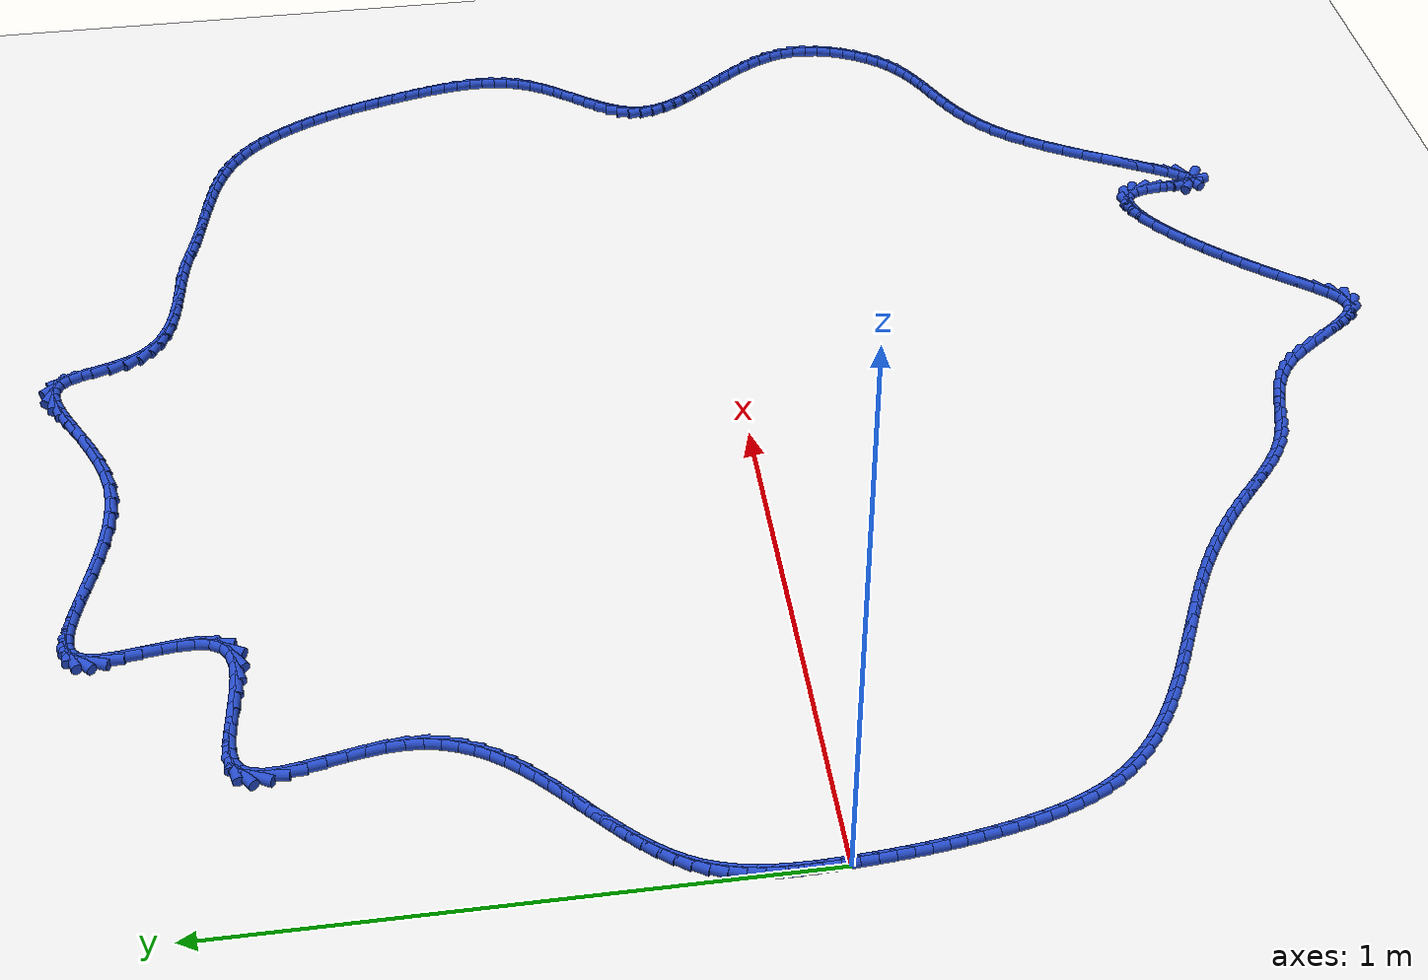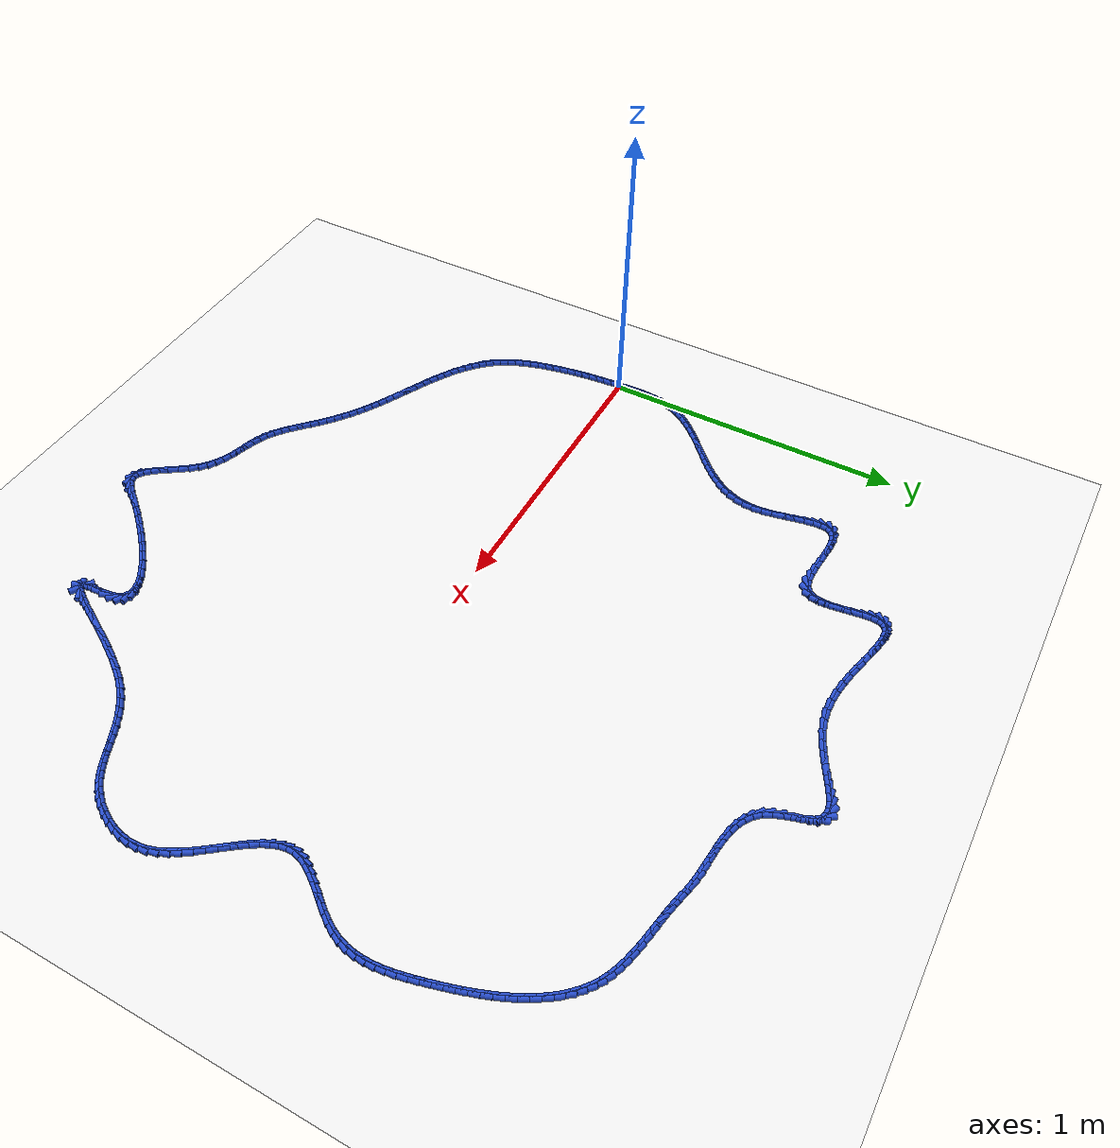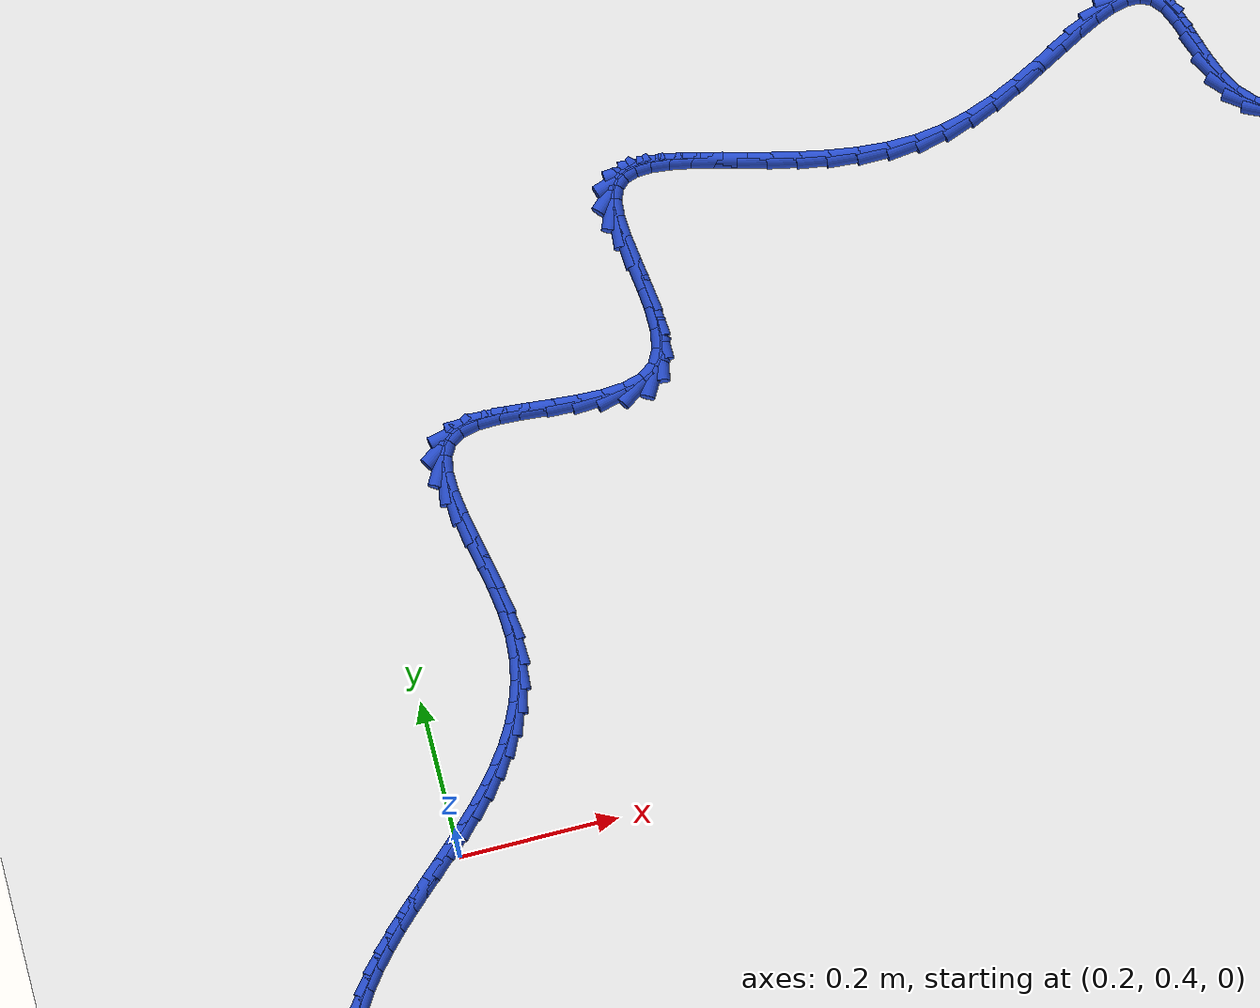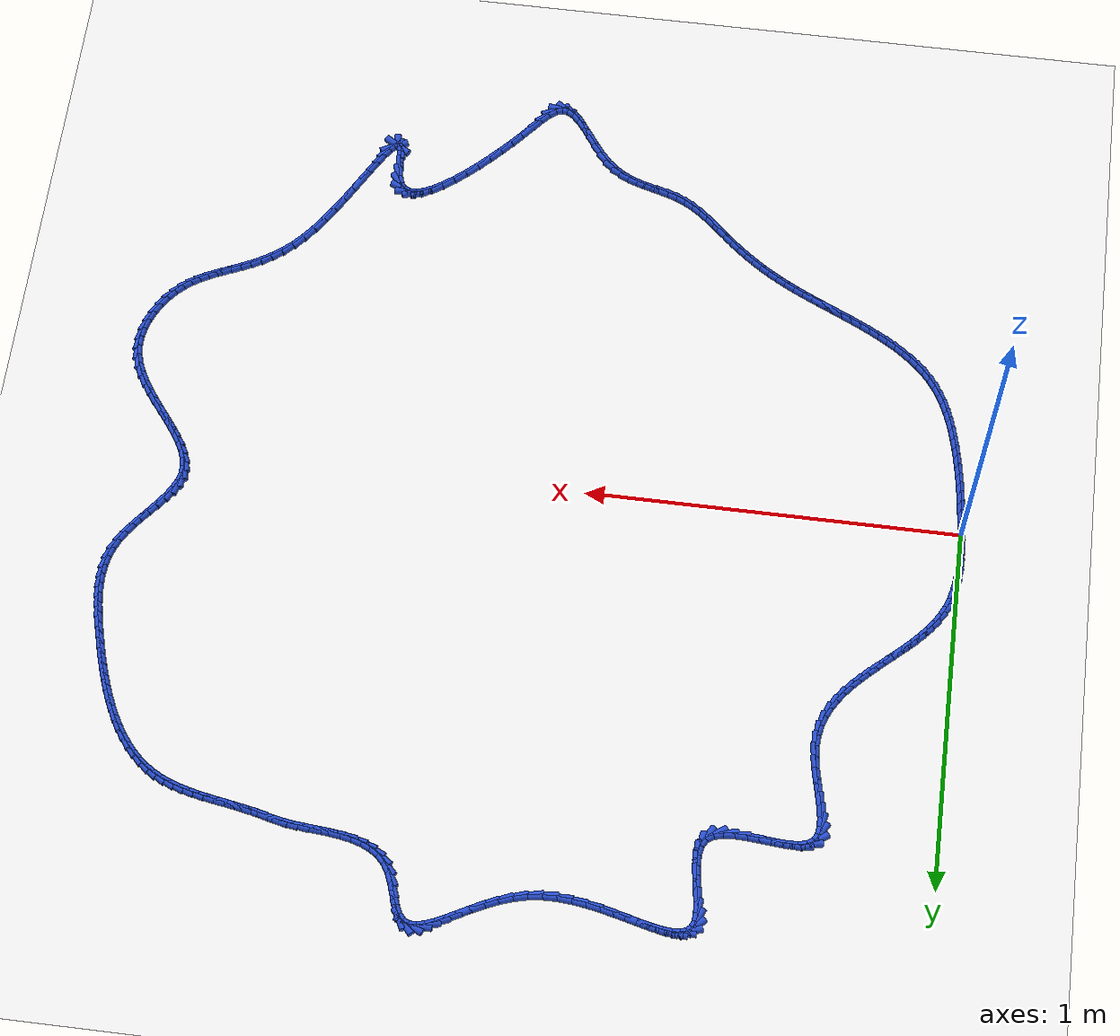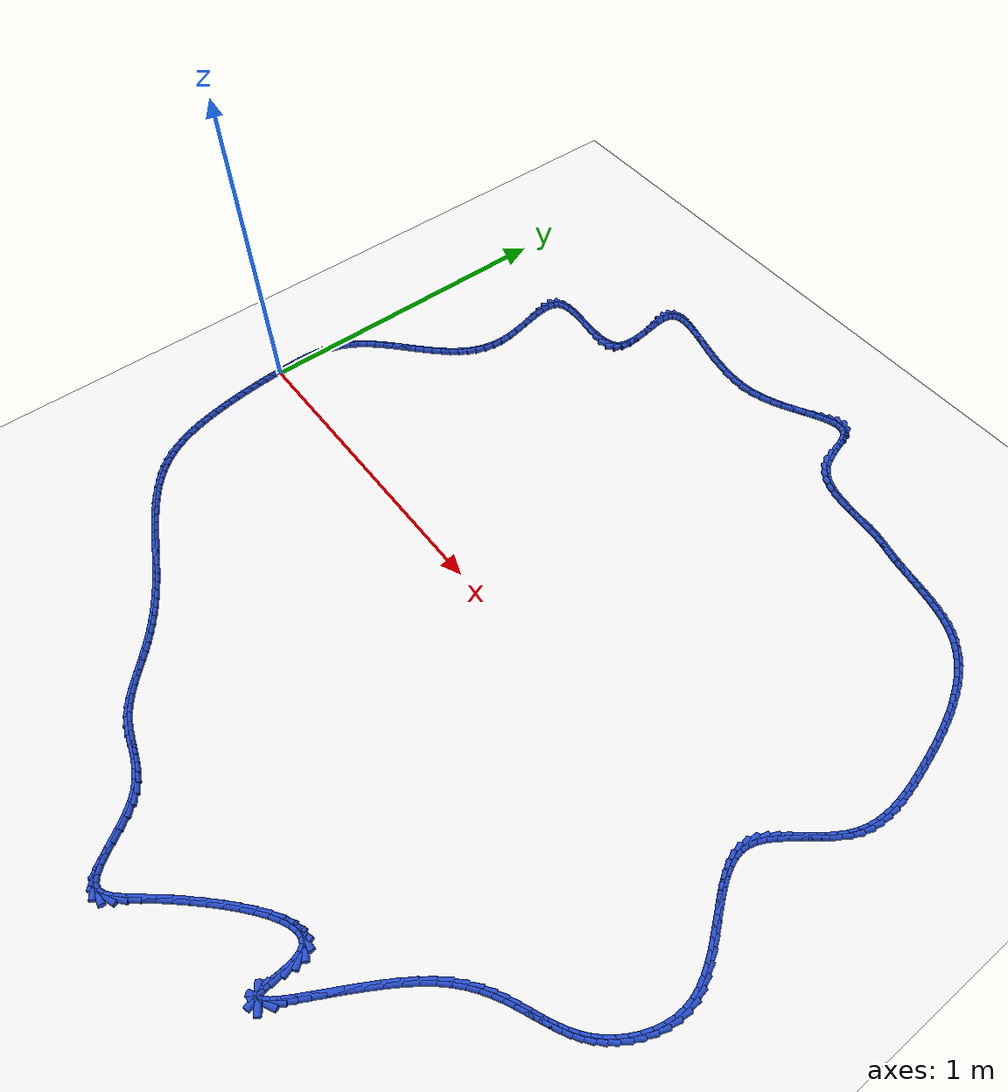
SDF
<sdf version="1.6">
 <world name="default">
  <light name="sun" type="directional">
   <pose>0 0 10 0 -0 0</pose>
   <diffuse>0.8 0.8 0.8 1</diffuse>
   <specular>0.2 0.2 0.2 1</specular>
   <attenuation>
    <range>1000</range>
    <constant>0.9</constant>
    <linear>0.01</linear>
    <quadratic>0.001</quadratic>
   </attenuation>
   <direction>-0.5 0.1 -0.9</direction>
  </light>
  <model name="ground_plane">
   <static>1</static>
   <link name="link">
    <collision name="collision">
     <geometry><plane><normal>0 0 1</normal><size>100 100</size></plane></geometry>
     <surface><friction><ode><mu>100</mu><mu2>50</mu2></ode></friction></surface>
    </collision>
    <visual name="visual">
     <cast_shadows>0</cast_shadows>
     <geometry><plane><normal>0 0 1</normal><size>100 100</size></plane></geometry>
     <material>
      <script><uri>file://media/materials/scripts/gazebo.material</uri><name>Gazebo/WhiteGlow</name></script>
     </material>
    </visual>
   </link>
  </model>
  <gravity>0 0 -9.8</gravity>
  <magnetic_field>6e-06 2.3e-05 -4.2e-05</magnetic_field>
  <atmosphere type="adiabatic"/>
  <physics name="default_physics" default="0" type="ode">
   <max_step_size>0.001</max_step_size>
   <real_time_factor>1</real_time_factor>
   <real_time_update_rate>1000</real_time_update_rate>
  </physics>
  <scene><ambient>0.4 0.4 0.4 1</ambient><background>0.7 0.7 0.7 1</background><shadows>1</shadows></scene>
  <spherical_coordinates>
   <surface_model>EARTH_WGS84</surface_model>
   <latitude_deg>0</latitude_deg>
   <longitude_deg>0</longitude_deg>
   <elevation>0</elevation>
   <heading_deg>0</heading_deg>
  </spherical_coordinates>
  <model name="line">
   <link name="link_0">
    <pose>2.8189256484623115e-17 4.85722573273506e-17 0.01 0 1.57 -1.5270184267594702</pose>
    <collision name="collision">
     <geometry><cylinder><radius>0.01</radius><length>0.08</length></cylinder></geometry>
    </collision>
    <visual name="visual">
     <material>
      <script><name>Gazebo/Blue</name><uri>file://media/materials/scripts/gazebo.material</uri></script>
     </material>
     <geometry><cylinder><radius>0.01</radius><length>0.08</length></cylinder></geometry>
    </visual>
   </link>
   <link name="link_1">
    <pose>-0.0012457737586339022 0.028438500070601964 0.01 0 1.57 -1.5487521793531875</pose>
    <collision name="collision">
     <geometry><cylinder><radius>0.01</radius><length>0.08</length></cylinder></geometry>
    </collision>
    <visual name="visual">
     <material>
      <script><name>Gazebo/Blue</name><uri>file://media/materials/scripts/gazebo.material</uri></script>
     </material>
     <geometry><cylinder><radius>0.01</radius><length>0.08</length></cylinder></geometry>
    </visual>
   </link>
   <link name="link_2">
    <pose>-0.0018765141941405029 0.05704646804013525 0.01 0 1.57 1.5607097423569645</pose>
    <collision name="collision">
     <geometry><cylinder><radius>0.01</radius><length>0.08</length></cylinder></geometry>
    </collision>
    <visual name="visual">
     <material>
      <script><name>Gazebo/Blue</name><uri>file://media/materials/scripts/gazebo.material</uri></script>
     </material>
     <geometry><cylinder><radius>0.01</radius><length>0.08</length></cylinder></geometry>
    </visual>
   </link>
   <link name="link_3">
    <pose>-0.001588317726900992 0.0856177545169355 0.01 0 1.57 1.5175069285638434</pose>
    <collision name="collision">
     <geometry><cylinder><radius>0.01</radius><length>0.08</length></cylinder></geometry>
    </collision>
    <visual name="visual">
     <material>
      <script><name>Gazebo/Blue</name><uri>file://media/materials/scripts/gazebo.material</uri></script>
     </material>
     <geometry><cylinder><radius>0.01</radius><length>0.08</length></cylinder></geometry>
    </visual>
   </link>
   <link name="link_4">
    <pose>-7.728077729658939e-05 0.11394621010933835 0.01 0 1.57 1.4622632989782698</pose>
    <collision name="collision">
     <geometry><cylinder><radius>0.01</radius><length>0.08</length></cylinder></geometry>
    </collision>
    <visual name="visual">
     <material>
      <script><name>Gazebo/Blue</name><uri>file://media/materials/scripts/gazebo.material</uri></script>
     </material>
     <geometry><cylinder><radius>0.01</radius><length>0.08</length></cylinder></geometry>
    </visual>
   </link>
   <link name="link_5">
    <pose>0.002960500234291487 0.14182568542567953 0.01 0 1.57 1.3938404987453474</pose>
    <collision name="collision">
     <geometry><cylinder><radius>0.01</radius><length>0.08</length></cylinder></geometry>
    </collision>
    <visual name="visual">
     <material>
      <script><name>Gazebo/Blue</name><uri>file://media/materials/scripts/gazebo.material</uri></script>
     </material>
     <geometry><cylinder><radius>0.01</radius><length>0.08</length></cylinder></geometry>
    </visual>
   </link>
   <link name="link_6">
    <pose>0.00782892888748202 0.16905003107429462 0.01 0 1.57 1.3111564111218528</pose>
    <collision name="collision">
     <geometry><cylinder><radius>0.01</radius><length>0.08</length></cylinder></geometry>
    </collision>
    <visual name="visual">
     <material>
      <script><name>Gazebo/Blue</name><uri>file://media/materials/scripts/gazebo.material</uri></script>
     </material>
     <geometry><cylinder><radius>0.01</radius><length>0.08</length></cylinder></geometry>
    </visual>
   </link>
   <link name="link_7">
    <pose>0.014831908761893782 0.19541309766351916 0.01 0 1.57 1.213566415298523</pose>
    <collision name="collision">
     <geometry><cylinder><radius>0.01</radius><length>0.08</length></cylinder></geometry>
    </collision>
    <visual name="visual">
     <material>
      <script><name>Gazebo/Blue</name><uri>file://media/materials/scripts/gazebo.material</uri></script>
     </material>
     <geometry><cylinder><radius>0.01</radius><length>0.08</length></cylinder></geometry>
    </visual>
   </link>
   <link name="link_8">
    <pose>0.024273343437145555 0.22070873580168898 0.01 0 1.57 1.1051298692728908</pose>
    <collision name="collision">
     <geometry><cylinder><radius>0.01</radius><length>0.08</length></cylinder></geometry>
    </collision>
    <visual name="visual">
     <material>
      <script><name>Gazebo/Blue</name><uri>file://media/materials/scripts/gazebo.material</uri></script>
     </material>
     <geometry><cylinder><radius>0.01</radius><length>0.08</length></cylinder></geometry>
    </visual>
   </link>
   <link name="link_9">
    <pose>0.03637018985321749 0.2447808110211887 0.01 0 1.57 1.0060598931638673</pose>
    <collision name="collision">
     <geometry><cylinder><radius>0.01</radius><length>0.08</length></cylinder></geometry>
    </collision>
    <visual name="visual">
     <material>
      <script><name>Gazebo/Blue</name><uri>file://media/materials/scripts/gazebo.material</uri></script>
     </material>
     <geometry><cylinder><radius>0.01</radius><length>0.08</length></cylinder></geometry>
    </visual>
   </link>
   <link name="link_10">
    <pose>0.050905483831939394 0.2677227963361615 0.01 0 1.57 0.9233946547981546</pose>
    <collision name="collision">
     <geometry><cylinder><radius>0.01</radius><length>0.08</length></cylinder></geometry>
    </collision>
    <visual name="visual">
     <material>
      <script><name>Gazebo/Blue</name><uri>file://media/materials/scripts/gazebo.material</uri></script>
     </material>
     <geometry><cylinder><radius>0.01</radius><length>0.08</length></cylinder></geometry>
    </visual>
   </link>
   <link name="link_11">
    <pose>0.06752716633747341 0.28970587632124006 0.01 0 1.57 0.8570658186349505</pose>
    <collision name="collision">
     <geometry><cylinder><radius>0.01</radius><length>0.08</length></cylinder></geometry>
    </collision>
    <visual name="visual">
     <material>
      <script><name>Gazebo/Blue</name><uri>file://media/materials/scripts/gazebo.material</uri></script>
     </material>
     <geometry><cylinder><radius>0.01</radius><length>0.08</length></cylinder></geometry>
    </visual>
   </link>
   <link name="link_12">
    <pose>0.08588313487057297 0.31090126055281836 0.01 0 1.57 0.8062485022180202</pose>
    <collision name="collision">
     <geometry><cylinder><radius>0.01</radius><length>0.08</length></cylinder></geometry>
    </collision>
    <visual name="visual">
     <material>
      <script><name>Gazebo/Blue</name><uri>file://media/materials/scripts/gazebo.material</uri></script>
     </material>
     <geometry><cylinder><radius>0.01</radius><length>0.08</length></cylinder></geometry>
    </visual>
   </link>
   <link name="link_13">
    <pose>0.10562128693199165 0.33148015860729013 0.01 0 1.57 0.7698839348173023</pose>
    <collision name="collision">
     <geometry><cylinder><radius>0.01</radius><length>0.08</length></cylinder></geometry>
    </collision>
    <visual name="visual">
     <material>
      <script><name>Gazebo/Blue</name><uri>file://media/materials/scripts/gazebo.material</uri></script>
     </material>
     <geometry><cylinder><radius>0.01</radius><length>0.08</length></cylinder></geometry>
    </visual>
   </link>
   <link name="link_14">
    <pose>0.12638952002248283 0.35161378006104876 0.01 0 1.57 0.7470045527305095</pose>
    <collision name="collision">
     <geometry><cylinder><radius>0.01</radius><length>0.08</length></cylinder></geometry>
    </collision>
    <visual name="visual">
     <material>
      <script><name>Gazebo/Blue</name><uri>file://media/materials/scripts/gazebo.material</uri></script>
     </material>
     <geometry><cylinder><radius>0.01</radius><length>0.08</length></cylinder></geometry>
    </visual>
   </link>
   <link name="link_15">
    <pose>0.14783573164280014 0.3714733344904882 0.01 0 1.57 0.7369062383043258</pose>
    <collision name="collision">
     <geometry><cylinder><radius>0.01</radius><length>0.08</length></cylinder></geometry>
    </collision>
    <visual name="visual">
     <material>
      <script><name>Gazebo/Blue</name><uri>file://media/materials/scripts/gazebo.material</uri></script>
     </material>
     <geometry><cylinder><radius>0.01</radius><length>0.08</length></cylinder></geometry>
    </visual>
   </link>
   <link name="link_16">
    <pose>0.16960781929369692 0.39123003147200197 0.01 0 1.57 0.7392253263858691</pose>
    <collision name="collision">
     <geometry><cylinder><radius>0.01</radius><length>0.08</length></cylinder></geometry>
    </collision>
    <visual name="visual">
     <material>
      <script><name>Gazebo/Blue</name><uri>file://media/materials/scripts/gazebo.material</uri></script>
     </material>
     <geometry><cylinder><radius>0.01</radius><length>0.08</length></cylinder></geometry>
    </visual>
   </link>
   <link name="link_17">
    <pose>0.19135368047592666 0.4110550805819838 0.01 0 1.57 0.7539614076946596</pose>
    <collision name="collision">
     <geometry><cylinder><radius>0.01</radius><length>0.08</length></cylinder></geometry>
    </collision>
    <visual name="visual">
     <material>
      <script><name>Gazebo/Blue</name><uri>file://media/materials/scripts/gazebo.material</uri></script>
     </material>
     <geometry><cylinder><radius>0.01</radius><length>0.08</length></cylinder></geometry>
    </visual>
   </link>
   <link name="link_18">
    <pose>0.212721212690243 0.43111969139682754 0.01 0 1.57 0.7814646180167457</pose>
    <collision name="collision">
     <geometry><cylinder><radius>0.01</radius><length>0.08</length></cylinder></geometry>
    </collision>
    <visual name="visual">
     <material>
      <script><name>Gazebo/Blue</name><uri>file://media/materials/scripts/gazebo.material</uri></script>
     </material>
     <geometry><cylinder><radius>0.01</radius><length>0.08</length></cylinder></geometry>
    </visual>
   </link>
   <link name="link_19">
    <pose>0.2333583134373992 0.4515950734929266 0.01 0 1.57 0.8223850987273342</pose>
    <collision name="collision">
     <geometry><cylinder><radius>0.01</radius><length>0.08</length></cylinder></geometry>
    </collision>
    <visual name="visual">
     <material>
      <script><name>Gazebo/Blue</name><uri>file://media/materials/scripts/gazebo.material</uri></script>
     </material>
     <geometry><cylinder><radius>0.01</radius><length>0.08</length></cylinder></geometry>
    </visual>
   </link>
   <link name="link_20">
    <pose>0.252912880218149 0.472652436446675 0.01 0 1.57 0.8775625224028165</pose>
    <collision name="collision">
     <geometry><cylinder><radius>0.01</radius><length>0.08</length></cylinder></geometry>
    </collision>
    <visual name="visual">
     <material>
      <script><name>Gazebo/Blue</name><uri>file://media/materials/scripts/gazebo.material</uri></script>
     </material>
     <geometry><cylinder><radius>0.01</radius><length>0.08</length></cylinder></geometry>
    </visual>
   </link>
   <link name="link_21">
    <pose>0.2710328105332457 0.4944629898344662 0.01 0 1.57 0.94781618550679</pose>
    <collision name="collision">
     <geometry><cylinder><radius>0.01</radius><length>0.08</length></cylinder></geometry>
    </collision>
    <visual name="visual">
     <material>
      <script><name>Gazebo/Blue</name><uri>file://media/materials/scripts/gazebo.material</uri></script>
     </material>
     <geometry><cylinder><radius>0.01</radius><length>0.08</length></cylinder></geometry>
    </visual>
   </link>
   <link name="link_22">
    <pose>0.2873660018834429 0.517197943232694 0.01 0 1.57 1.0335915602208208</pose>
    <collision name="collision">
     <geometry><cylinder><radius>0.01</radius><length>0.08</length></cylinder></geometry>
    </collision>
    <visual name="visual">
     <material>
      <script><name>Gazebo/Blue</name><uri>file://media/materials/scripts/gazebo.material</uri></script>
     </material>
     <geometry><cylinder><radius>0.01</radius><length>0.08</length></cylinder></geometry>
    </visual>
   </link>
   <link name="link_23">
    <pose>0.3015603517694939 0.5410285062177519 0.01 0 1.57 1.1344540504657912</pose>
    <collision name="collision">
     <geometry><cylinder><radius>0.01</radius><length>0.08</length></cylinder></geometry>
    </collision>
    <visual name="visual">
     <material>
      <script><name>Gazebo/Blue</name><uri>file://media/materials/scripts/gazebo.material</uri></script>
     </material>
     <geometry><cylinder><radius>0.01</radius><length>0.08</length></cylinder></geometry>
    </visual>
   </link>
   <link name="link_24">
    <pose>0.3132637576921525 0.5661258883660338 0.01 0 1.57 1.2485295607187281</pose>
    <collision name="collision">
     <geometry><cylinder><radius>0.01</radius><length>0.08</length></cylinder></geometry>
    </collision>
    <visual name="visual">
     <material>
      <script><name>Gazebo/Blue</name><uri>file://media/materials/scripts/gazebo.material</uri></script>
     </material>
     <geometry><cylinder><radius>0.01</radius><length>0.08</length></cylinder></geometry>
    </visual>
   </link>
   <link name="link_25">
    <pose>0.3221241171521718 0.5926612992539333 0.01 0 1.57 1.3721615763816375</pose>
    <collision name="collision">
     <geometry><cylinder><radius>0.01</radius><length>0.08</length></cylinder></geometry>
    </collision>
    <visual name="visual">
     <material>
      <script><name>Gazebo/Blue</name><uri>file://media/materials/scripts/gazebo.material</uri></script>
     </material>
     <geometry><cylinder><radius>0.01</radius><length>0.08</length></cylinder></geometry>
    </visual>
   </link>
   <link name="link_26">
    <pose>0.3277893276503056 0.6208059484578441 0.01 0 1.57 1.500138803783585</pose>
    <collision name="collision">
     <geometry><cylinder><radius>0.01</radius><length>0.08</length></cylinder></geometry>
    </collision>
    <visual name="visual">
     <material>
      <script><name>Gazebo/Blue</name><uri>file://media/materials/scripts/gazebo.material</uri></script>
     </material>
     <geometry><cylinder><radius>0.01</radius><length>0.08</length></cylinder></geometry>
    </visual>
   </link>
   <link name="link_27">
    <pose>0.3299072866873071 0.6507310455541597 0.01 0 1.57 -1.5180559374970308</pose>
    <collision name="collision">
     <geometry><cylinder><radius>0.01</radius><length>0.08</length></cylinder></geometry>
    </collision>
    <visual name="visual">
     <material>
      <script><name>Gazebo/Blue</name><uri>file://media/materials/scripts/gazebo.material</uri></script>
     </material>
     <geometry><cylinder><radius>0.01</radius><length>0.08</length></cylinder></geometry>
    </visual>
   </link>
   <link name="link_28">
    <pose>0.32822816356438206 0.6825390394324435 0.01 0 1.57 -1.4284534308537788</pose>
    <collision name="collision">
     <geometry><cylinder><radius>0.01</radius><length>0.08</length></cylinder></geometry>
    </collision>
    <visual name="visual">
     <material>
      <script><name>Gazebo/Blue</name><uri>file://media/materials/scripts/gazebo.material</uri></script>
     </material>
     <geometry><cylinder><radius>0.01</radius><length>0.08</length></cylinder></geometry>
    </visual>
   </link>
   <link name="link_29">
    <pose>0.32347932503253163 0.7156753770763458 0.01 0 1.57 -1.378004912428191</pose>
    <collision name="collision">
     <geometry><cylinder><radius>0.01</radius><length>0.08</length></cylinder></geometry>
    </collision>
    <visual name="visual">
     <material>
      <script><name>Gazebo/Blue</name><uri>file://media/materials/scripts/gazebo.material</uri></script>
     </material>
     <geometry><cylinder><radius>0.01</radius><length>0.08</length></cylinder></geometry>
    </visual>
   </link>
   <link name="link_30">
    <pose>0.31693073999039123 0.7492206962436859 0.01 0 1.57 -1.3598628349203699</pose>
    <collision name="collision">
     <geometry><cylinder><radius>0.01</radius><length>0.08</length></cylinder></geometry>
    </collision>
    <visual name="visual">
     <material>
      <script><name>Gazebo/Blue</name><uri>file://media/materials/scripts/gazebo.material</uri></script>
     </material>
     <geometry><cylinder><radius>0.01</radius><length>0.08</length></cylinder></geometry>
    </visual>
   </link>
   <link name="link_31">
    <pose>0.3098581830123506 0.7822517313459958 0.01 0 1.57 -1.373338155935342</pose>
    <collision name="collision">
     <geometry><cylinder><radius>0.01</radius><length>0.08</length></cylinder></geometry>
    </collision>
    <visual name="visual">
     <material>
      <script><name>Gazebo/Blue</name><uri>file://media/materials/scripts/gazebo.material</uri></script>
     </material>
     <geometry><cylinder><radius>0.01</radius><length>0.08</length></cylinder></geometry>
    </visual>
   </link>
   <link name="link_32">
    <pose>0.3035374286727999 0.8138452167948091 0.01 0 1.57 -1.4249764397873044</pose>
    <collision name="collision">
     <geometry><cylinder><radius>0.01</radius><length>0.08</length></cylinder></geometry>
    </collision>
    <visual name="visual">
     <material>
      <script><name>Gazebo/Blue</name><uri>file://media/materials/scripts/gazebo.material</uri></script>
     </material>
     <geometry><cylinder><radius>0.01</radius><length>0.08</length></cylinder></geometry>
    </visual>
   </link>
   <link name="link_33">
    <pose>0.29924425154612905 0.8430778870016579 0.01 0 1.57 -1.5326691804968642</pose>
    <collision name="collision">
     <geometry><cylinder><radius>0.01</radius><length>0.08</length></cylinder></geometry>
    </collision>
    <visual name="visual">
     <material>
      <script><name>Gazebo/Blue</name><uri>file://media/materials/scripts/gazebo.material</uri></script>
     </material>
     <geometry><cylinder><radius>0.01</radius><length>0.08</length></cylinder></geometry>
    </visual>
   </link>
   <link name="link_34">
    <pose>0.29825442620672804 0.8690264763780754 0.01 0 1.57 1.4071803383604398</pose>
    <collision name="collision">
     <geometry><cylinder><radius>0.01</radius><length>0.08</length></cylinder></geometry>
    </collision>
    <visual name="visual">
     <material>
      <script><name>Gazebo/Blue</name><uri>file://media/materials/scripts/gazebo.material</uri></script>
     </material>
     <geometry><cylinder><radius>0.01</radius><length>0.08</length></cylinder></geometry>
    </visual>
   </link>
   <link name="link_35">
    <pose>0.3018437272289866 0.8907677193355936 0.01 0 1.57 1.053812542477235</pose>
    <collision name="collision">
     <geometry><cylinder><radius>0.01</radius><length>0.08</length></cylinder></geometry>
    </collision>
    <visual name="visual">
     <material>
      <script><name>Gazebo/Blue</name><uri>file://media/materials/scripts/gazebo.material</uri></script>
     </material>
     <geometry><cylinder><radius>0.01</radius><length>0.08</length></cylinder></geometry>
    </visual>
   </link>
   <link name="link_36">
    <pose>0.311287929187295 0.9073783502857461 0.01 0 1.57 0.5731029123995073</pose>
    <collision name="collision">
     <geometry><cylinder><radius>0.01</radius><length>0.08</length></cylinder></geometry>
    </collision>
    <visual name="visual">
     <material>
      <script><name>Gazebo/Blue</name><uri>file://media/materials/scripts/gazebo.material</uri></script>
     </material>
     <geometry><cylinder><radius>0.01</radius><length>0.08</length></cylinder></geometry>
    </visual>
   </link>
   <link name="link_37">
    <pose>0.3277672467987188 0.9180133603840078 0.01 0 1.57 0.2155673965269952</pose>
    <collision name="collision">
     <geometry><cylinder><radius>0.01</radius><length>0.08</length></cylinder></geometry>
    </collision>
    <visual name="visual">
     <material>
      <script><name>Gazebo/Blue</name><uri>file://media/materials/scripts/gazebo.material</uri></script>
     </material>
     <geometry><cylinder><radius>0.01</radius><length>0.08</length></cylinder></geometry>
    </visual>
   </link>
   <link name="link_38">
    <pose>0.3509270627931485 0.9230846592993166 0.01 0 1.57 0.0330174391332561</pose>
    <collision name="collision">
     <geometry><cylinder><radius>0.01</radius><length>0.08</length></cylinder></geometry>
    </collision>
    <visual name="visual">
     <material>
      <script><name>Gazebo/Blue</name><uri>file://media/materials/scripts/gazebo.material</uri></script>
     </material>
     <geometry><cylinder><radius>0.01</radius><length>0.08</length></cylinder></geometry>
    </visual>
   </link>
   <link name="link_39">
    <pose>0.37917514242082 0.9240176776174045 0.01 0 1.57 -0.05516395849247522</pose>
    <collision name="collision">
     <geometry><cylinder><radius>0.01</radius><length>0.08</length></cylinder></geometry>
    </collision>
    <visual name="visual">
     <material>
      <script><name>Gazebo/Blue</name><uri>file://media/materials/scripts/gazebo.material</uri></script>
     </material>
     <geometry><cylinder><radius>0.01</radius><length>0.08</length></cylinder></geometry>
    </visual>
   </link>
   <link name="link_40">
    <pose>0.4108839985320772 0.9222667151386378 0.01 0 1.57 -0.08862983513350375</pose>
    <collision name="collision">
     <geometry><cylinder><radius>0.01</radius><length>0.08</length></cylinder></geometry>
    </collision>
    <visual name="visual">
     <material>
      <script><name>Gazebo/Blue</name><uri>file://media/materials/scripts/gazebo.material</uri></script>
     </material>
     <geometry><cylinder><radius>0.01</radius><length>0.08</length></cylinder></geometry>
    </visual>
   </link>
   <link name="link_41">
    <pose>0.44442614397726493 0.9192860716633839 0.01 0 1.57 -0.08148413370866106</pose>
    <collision name="collision">
     <geometry><cylinder><radius>0.01</radius><length>0.08</length></cylinder></geometry>
    </collision>
    <visual name="visual">
     <material>
      <script><name>Gazebo/Blue</name><uri>file://media/materials/scripts/gazebo.material</uri></script>
     </material>
     <geometry><cylinder><radius>0.01</radius><length>0.08</length></cylinder></geometry>
    </visual>
   </link>
   <link name="link_42">
    <pose>0.47817409160672697 0.9165300469920091 0.01 0 1.57 -0.03330752268638558</pose>
    <collision name="collision">
     <geometry><cylinder><radius>0.01</radius><length>0.08</length></cylinder></geometry>
    </collision>
    <visual name="visual">
     <material>
      <script><name>Gazebo/Blue</name><uri>file://media/materials/scripts/gazebo.material</uri></script>
     </material>
     <geometry><cylinder><radius>0.01</radius><length>0.08</length></cylinder></geometry>
    </visual>
   </link>
   <link name="link_43">
    <pose>0.510500354270808 0.9154529409248807 0.01 0 1.57 0.07011427377807904</pose>
    <collision name="collision">
     <geometry><cylinder><radius>0.01</radius><length>0.08</length></cylinder></geometry>
    </collision>
    <visual name="visual">
     <material>
      <script><name>Gazebo/Blue</name><uri>file://media/materials/scripts/gazebo.material</uri></script>
     </material>
     <geometry><cylinder><radius>0.01</radius><length>0.08</length></cylinder></geometry>
    </visual>
   </link>
   <link name="link_44">
    <pose>0.5397774448198527 0.9175090532623656 0.01 0 1.57 0.2637691991494465</pose>
    <collision name="collision">
     <geometry><cylinder><radius>0.01</radius><length>0.08</length></cylinder></geometry>
    </collision>
    <visual name="visual">
     <material>
      <script><name>Gazebo/Blue</name><uri>file://media/materials/scripts/gazebo.material</uri></script>
     </material>
     <geometry><cylinder><radius>0.01</radius><length>0.08</length></cylinder></geometry>
    </visual>
   </link>
   <link name="link_45">
    <pose>0.5643778761042046 0.9241526838048302 0.01 0 1.57 0.6062385637772806</pose>
    <collision name="collision">
     <geometry><cylinder><radius>0.01</radius><length>0.08</length></cylinder></geometry>
    </collision>
    <visual name="visual">
     <material>
      <script><name>Gazebo/Blue</name><uri>file://media/materials/scripts/gazebo.material</uri></script>
     </material>
     <geometry><cylinder><radius>0.01</radius><length>0.08</length></cylinder></geometry>
    </visual>
   </link>
   <link name="link_46">
    <pose>0.5826741609742089 0.9368381323526419 0.01 0 1.57 1.0689722509299344</pose>
    <collision name="collision">
     <geometry><cylinder><radius>0.01</radius><length>0.08</length></cylinder></geometry>
    </collision>
    <visual name="visual">
     <material>
      <script><name>Gazebo/Blue</name><uri>file://media/materials/scripts/gazebo.material</uri></script>
     </material>
     <geometry><cylinder><radius>0.01</radius><length>0.08</length></cylinder></geometry>
    </visual>
   </link>
   <link name="link_47">
    <pose>0.5934992053485492 0.9565676216216292 0.01 0 1.57 1.400498101186811</pose>
    <collision name="collision">
     <geometry><cylinder><radius>0.01</radius><length>0.08</length></cylinder></geometry>
    </collision>
    <visual name="visual">
     <material>
      <script><name>Gazebo/Blue</name><uri>file://media/materials/scripts/gazebo.material</uri></script>
     </material>
     <geometry><cylinder><radius>0.01</radius><length>0.08</length></cylinder></geometry>
    </visual>
   </link>
   <link name="link_48">
    <pose>0.5979015104187928 0.982167798889243 0.01 0 1.57 -1.5604646393977564</pose>
    <collision name="collision">
     <geometry><cylinder><radius>0.01</radius><length>0.08</length></cylinder></geometry>
    </collision>
    <visual name="visual">
     <material>
      <script><name>Gazebo/Blue</name><uri>file://media/materials/scripts/gazebo.material</uri></script>
     </material>
     <geometry><cylinder><radius>0.01</radius><length>0.08</length></cylinder></geometry>
    </visual>
   </link>
   <link name="link_49">
    <pose>0.5975952281650001 1.0118116841555547 0.01 0 1.57 -1.4675695189759064</pose>
    <collision name="collision">
     <geometry><cylinder><radius>0.01</radius><length>0.08</length></cylinder></geometry>
    </collision>
    <visual name="visual">
     <material>
      <script><name>Gazebo/Blue</name><uri>file://media/materials/scripts/gazebo.material</uri></script>
     </material>
     <geometry><cylinder><radius>0.01</radius><length>0.08</length></cylinder></geometry>
    </visual>
   </link>
   <link name="link_50">
    <pose>0.5942946401174354 1.0436721702104728 0.01 0 1.57 -1.4297054764931552</pose>
    <collision name="collision">
     <geometry><cylinder><radius>0.01</radius><length>0.08</length></cylinder></geometry>
    </collision>
    <visual name="visual">
     <material>
      <script><name>Gazebo/Blue</name><uri>file://media/materials/scripts/gazebo.material</uri></script>
     </material>
     <geometry><cylinder><radius>0.01</radius><length>0.08</length></cylinder></geometry>
    </visual>
   </link>
   <link name="link_51">
    <pose>0.5897140278063623 1.0759221498439033 0.01 0 1.57 -1.437031999981583</pose>
    <collision name="collision">
     <geometry><cylinder><radius>0.01</radius><length>0.08</length></cylinder></geometry>
    </collision>
    <visual name="visual">
     <material>
      <script><name>Gazebo/Blue</name><uri>file://media/materials/scripts/gazebo.material</uri></script>
     </material>
     <geometry><cylinder><radius>0.01</radius><length>0.08</length></cylinder></geometry>
    </visual>
   </link>
   <link name="link_52">
    <pose>0.5855676727620449 1.1067345158457556 0.01 0 1.57 -1.4984008548374255</pose>
    <collision name="collision">
     <geometry><cylinder><radius>0.01</radius><length>0.08</length></cylinder></geometry>
    </collision>
    <visual name="visual">
     <material>
      <script><name>Gazebo/Blue</name><uri>file://media/materials/scripts/gazebo.material</uri></script>
     </material>
     <geometry><cylinder><radius>0.01</radius><length>0.08</length></cylinder></geometry>
    </visual>
   </link>
   <link name="link_53">
    <pose>0.5835698565147471 1.1342821610059355 0.01 0 1.57 1.4880102411819423</pose>
    <collision name="collision">
     <geometry><cylinder><radius>0.01</radius><length>0.08</length></cylinder></geometry>
    </collision>
    <visual name="visual">
     <material>
      <script><name>Gazebo/Blue</name><uri>file://media/materials/scripts/gazebo.material</uri></script>
     </material>
     <geometry><cylinder><radius>0.01</radius><length>0.08</length></cylinder></geometry>
    </visual>
   </link>
   <link name="link_54">
    <pose>0.5854333013477845 1.156739870062657 0.01 0 1.57 1.169242942604346</pose>
    <collision name="collision">
     <geometry><cylinder><radius>0.01</radius><length>0.08</length></cylinder></geometry>
    </collision>
    <visual name="visual">
     <material>
      <script><name>Gazebo/Blue</name><uri>file://media/materials/scripts/gazebo.material</uri></script>
     </material>
     <geometry><cylinder><radius>0.01</radius><length>0.08</length></cylinder></geometry>
    </visual>
   </link>
   <link name="link_55">
    <pose>0.5923179008458157 1.172953215226747 0.01 0 1.57 0.7301037879904235</pose>
    <collision name="collision">
     <geometry><cylinder><radius>0.01</radius><length>0.08</length></cylinder></geometry>
    </collision>
    <visual name="visual">
     <material>
      <script><name>Gazebo/Blue</name><uri>file://media/materials/scripts/gazebo.material</uri></script>
     </material>
     <geometry><cylinder><radius>0.01</radius><length>0.08</length></cylinder></geometry>
    </visual>
   </link>
   <link name="link_56">
    <pose>0.6040173656679337 1.1834254583224633 0.01 0 1.57 0.32839301494931356</pose>
    <collision name="collision">
     <geometry><cylinder><radius>0.01</radius><length>0.08</length></cylinder></geometry>
    </collision>
    <visual name="visual">
     <material>
      <script><name>Gazebo/Blue</name><uri>file://media/materials/scripts/gazebo.material</uri></script>
     </material>
     <geometry><cylinder><radius>0.01</radius><length>0.08</length></cylinder></geometry>
    </visual>
   </link>
   <link name="link_57">
    <pose>0.6201180577869234 1.1889114524926327 0.01 0 1.57 0.06237322992467666</pose>
    <collision name="collision">
     <geometry><cylinder><radius>0.01</radius><length>0.08</length></cylinder></geometry>
    </collision>
    <visual name="visual">
     <material>
      <script><name>Gazebo/Blue</name><uri>file://media/materials/scripts/gazebo.material</uri></script>
     </material>
     <geometry><cylinder><radius>0.01</radius><length>0.08</length></cylinder></geometry>
    </visual>
   </link>
   <link name="link_58">
    <pose>0.6402063391755705 1.1901660508800822 0.01 0 1.57 -0.09362801122148666</pose>
    <collision name="collision">
     <geometry><cylinder><radius>0.01</radius><length>0.08</length></cylinder></geometry>
    </collision>
    <visual name="visual">
     <material>
      <script><name>Gazebo/Blue</name><uri>file://media/materials/scripts/gazebo.material</uri></script>
     </material>
     <geometry><cylinder><radius>0.01</radius><length>0.08</length></cylinder></geometry>
    </visual>
   </link>
   <link name="link_59">
    <pose>0.6638685718066603 1.1879441066276388 0.01 0 1.57 -0.18226344772969358</pose>
    <collision name="collision">
     <geometry><cylinder><radius>0.01</radius><length>0.08</length></cylinder></geometry>
    </collision>
    <visual name="visual">
     <material>
      <script><name>Gazebo/Blue</name><uri>file://media/materials/scripts/gazebo.material</uri></script>
     </material>
     <geometry><cylinder><radius>0.01</radius><length>0.08</length></cylinder></geometry>
    </visual>
   </link>
   <link name="link_60">
    <pose>0.6906911176529775 1.1830004728781294 0.01 0 1.57 -0.22958422991078015</pose>
    <collision name="collision">
     <geometry><cylinder><radius>0.01</radius><length>0.08</length></cylinder></geometry>
    </collision>
    <visual name="visual">
     <material>
      <script><name>Gazebo/Blue</name><uri>file://media/materials/scripts/gazebo.material</uri></script>
     </material>
     <geometry><cylinder><radius>0.01</radius><length>0.08</length></cylinder></geometry>
    </visual>
   </link>
   <link name="link_61">
    <pose>0.7202603386873081 1.1760900027743808 0.01 0 1.57 -0.24930744057180185</pose>
    <collision name="collision">
     <geometry><cylinder><radius>0.01</radius><length>0.08</length></cylinder></geometry>
    </collision>
    <visual name="visual">
     <material>
      <script><name>Gazebo/Blue</name><uri>file://media/materials/scripts/gazebo.material</uri></script>
     </material>
     <geometry><cylinder><radius>0.01</radius><length>0.08</length></cylinder></geometry>
    </visual>
   </link>
   <link name="link_62">
    <pose>0.752162596882437 1.16796754945922 0.01 0 1.57 -0.24843099723452633</pose>
    <collision name="collision">
     <geometry><cylinder><radius>0.01</radius><length>0.08</length></cylinder></geometry>
    </collision>
    <visual name="visual">
     <material>
      <script><name>Gazebo/Blue</name><uri>file://media/materials/scripts/gazebo.material</uri></script>
     </material>
     <geometry><cylinder><radius>0.01</radius><length>0.08</length></cylinder></geometry>
    </visual>
   </link>
   <link name="link_63">
    <pose>0.7859842542111501 1.159387966075474 0.01 0 1.57 -0.23027316106922283</pose>
    <collision name="collision">
     <geometry><cylinder><radius>0.01</radius><length>0.08</length></cylinder></geometry>
    </collision>
    <visual name="visual">
     <material>
      <script><name>Gazebo/Blue</name><uri>file://media/materials/scripts/gazebo.material</uri></script>
     </material>
     <geometry><cylinder><radius>0.01</radius><length>0.08</length></cylinder></geometry>
    </visual>
   </link>
   <link name="link_64">
    <pose>0.821311672646232 1.1511061057659697 0.01 0 1.57 -0.19595297176354545</pose>
    <collision name="collision">
     <geometry><cylinder><radius>0.01</radius><length>0.08</length></cylinder></geometry>
    </collision>
    <visual name="visual">
     <material>
      <script><name>Gazebo/Blue</name><uri>file://media/materials/scripts/gazebo.material</uri></script>
     </material>
     <geometry><cylinder><radius>0.01</radius><length>0.08</length></cylinder></geometry>
    </visual>
   </link>
   <link name="link_65">
    <pose>0.8577312141604678 1.1438768216735338 0.01 0 1.57 -0.14512197979115246</pose>
    <collision name="collision">
     <geometry><cylinder><radius>0.01</radius><length>0.08</length></cylinder></geometry>
    </collision>
    <visual name="visual">
     <material>
      <script><name>Gazebo/Blue</name><uri>file://media/materials/scripts/gazebo.material</uri></script>
     </material>
     <geometry><cylinder><radius>0.01</radius><length>0.08</length></cylinder></geometry>
    </visual>
   </link>
   <link name="link_66">
    <pose>0.8948292407266442 1.1384549669409936 0.01 0 1.57 -0.07638621077039279</pose>
    <collision name="collision">
     <geometry><cylinder><radius>0.01</radius><length>0.08</length></cylinder></geometry>
    </collision>
    <visual name="visual">
     <material>
      <script><name>Gazebo/Blue</name><uri>file://media/materials/scripts/gazebo.material</uri></script>
     </material>
     <geometry><cylinder><radius>0.01</radius><length>0.08</length></cylinder></geometry>
    </visual>
   </link>
   <link name="link_67">
    <pose>0.9321921143175452 1.135595394711176 0.01 0 1.57 0.012294817665572024</pose>
    <collision name="collision">
     <geometry><cylinder><radius>0.01</radius><length>0.08</length></cylinder></geometry>
    </collision>
    <visual name="visual">
     <material>
      <script><name>Gazebo/Blue</name><uri>file://media/materials/scripts/gazebo.material</uri></script>
     </material>
     <geometry><cylinder><radius>0.01</radius><length>0.08</length></cylinder></geometry>
    </visual>
   </link>
   <link name="link_68">
    <pose>0.9694061969059568 1.1360529581269074 0.01 0 1.57 0.12295039126527911</pose>
    <collision name="collision">
     <geometry><cylinder><radius>0.01</radius><length>0.08</length></cylinder></geometry>
    </collision>
    <visual name="visual">
     <material>
      <script><name>Gazebo/Blue</name><uri>file://media/materials/scripts/gazebo.material</uri></script>
     </material>
     <geometry><cylinder><radius>0.01</radius><length>0.08</length></cylinder></geometry>
    </visual>
   </link>
   <link name="link_69">
    <pose>1.0060578940600193 1.140582143929037 0.01 0 1.57 0.24500196113888262</pose>
    <collision name="collision">
     <geometry><cylinder><radius>0.01</radius><length>0.08</length></cylinder></geometry>
    </collision>
    <visual name="visual">
     <material>
      <script><name>Gazebo/Blue</name><uri>file://media/materials/scripts/gazebo.material</uri></script>
     </material>
     <geometry><cylinder><radius>0.01</radius><length>0.08</length></cylinder></geometry>
    </visual>
   </link>
   <link name="link_70">
    <pose>1.041783929180414 1.149514537081482 0.01 0 1.57 0.3450268204243644</pose>
    <collision name="collision">
     <geometry><cylinder><radius>0.01</radius><length>0.08</length></cylinder></geometry>
    </collision>
    <visual name="visual">
     <material>
      <script><name>Gazebo/Blue</name><uri>file://media/materials/scripts/gazebo.material</uri></script>
     </material>
     <geometry><cylinder><radius>0.01</radius><length>0.08</length></cylinder></geometry>
    </visual>
   </link>
   <link name="link_71">
    <pose>1.0763682636553344 1.1619442446321067 0.01 0 1.57 0.41864341282051465</pose>
    <collision name="collision">
     <geometry><cylinder><radius>0.01</radius><length>0.08</length></cylinder></geometry>
    </collision>
    <visual name="visual">
     <material>
      <script><name>Gazebo/Blue</name><uri>file://media/materials/scripts/gazebo.material</uri></script>
     </material>
     <geometry><cylinder><radius>0.01</radius><length>0.08</length></cylinder></geometry>
    </visual>
   </link>
   <link name="link_72">
    <pose>1.1096216483466217 1.1767402185408755 0.01 0 1.57 0.4677885761827647</pose>
    <collision name="collision">
     <geometry><cylinder><radius>0.01</radius><length>0.08</length></cylinder></geometry>
    </collision>
    <visual name="visual">
     <material>
      <script><name>Gazebo/Blue</name><uri>file://media/materials/scripts/gazebo.material</uri></script>
     </material>
     <geometry><cylinder><radius>0.01</radius><length>0.08</length></cylinder></geometry>
    </visual>
   </link>
   <link name="link_73">
    <pose>1.1413548341161175 1.192771410767753 0.01 0 1.57 0.49313372586930476</pose>
    <collision name="collision">
     <geometry><cylinder><radius>0.01</radius><length>0.08</length></cylinder></geometry>
    </collision>
    <visual name="visual">
     <material>
      <script><name>Gazebo/Blue</name><uri>file://media/materials/scripts/gazebo.material</uri></script>
     </material>
     <geometry><cylinder><radius>0.01</radius><length>0.08</length></cylinder></geometry>
    </visual>
   </link>
   <link name="link_74">
    <pose>1.1713785718256622 1.2089067732727026 0.01 0 1.57 0.49295495261555883</pose>
    <collision name="collision">
     <geometry><cylinder><radius>0.01</radius><length>0.08</length></cylinder></geometry>
    </collision>
    <visual name="visual">
     <material>
      <script><name>Gazebo/Blue</name><uri>file://media/materials/scripts/gazebo.material</uri></script>
     </material>
     <geometry><cylinder><radius>0.01</radius><length>0.08</length></cylinder></geometry>
    </visual>
   </link>
   <link name="link_75">
    <pose>1.199503612337097 1.224015258015689 0.01 0 1.57 0.4615564652339835</pose>
    <collision name="collision">
     <geometry><cylinder><radius>0.01</radius><length>0.08</length></cylinder></geometry>
    </collision>
    <visual name="visual">
     <material>
      <script><name>Gazebo/Blue</name><uri>file://media/materials/scripts/gazebo.material</uri></script>
     </material>
     <geometry><cylinder><radius>0.01</radius><length>0.08</length></cylinder></geometry>
    </visual>
   </link>
   <link name="link_76">
    <pose>1.2255407065122632 1.2369658169566768 0.01 0 1.57 0.38621231644863746</pose>
    <collision name="collision">
     <geometry><cylinder><radius>0.01</radius><length>0.08</length></cylinder></geometry>
    </collision>
    <visual name="visual">
     <material>
      <script><name>Gazebo/Blue</name><uri>file://media/materials/scripts/gazebo.material</uri></script>
     </material>
     <geometry><cylinder><radius>0.01</radius><length>0.08</length></cylinder></geometry>
    </visual>
   </link>
   <link name="link_77">
    <pose>1.249300605213002 1.24662740205563 0.01 0 1.57 0.24135981206605966</pose>
    <collision name="collision">
     <geometry><cylinder><radius>0.01</radius><length>0.08</length></cylinder></geometry>
    </collision>
    <visual name="visual">
     <material>
      <script><name>Gazebo/Blue</name><uri>file://media/materials/scripts/gazebo.material</uri></script>
     </material>
     <geometry><cylinder><radius>0.01</radius><length>0.08</length></cylinder></geometry>
    </visual>
   </link>
   <link name="link_78">
    <pose>1.2705940593011547 1.251868965272513 0.01 0 1.57 -0.016604906011673547</pose>
    <collision name="collision">
     <geometry><cylinder><radius>0.01</radius><length>0.08</length></cylinder></geometry>
    </collision>
    <visual name="visual">
     <material>
      <script><name>Gazebo/Blue</name><uri>file://media/materials/scripts/gazebo.material</uri></script>
     </material>
     <geometry><cylinder><radius>0.01</radius><length>0.08</length></cylinder></geometry>
    </visual>
   </link>
   <link name="link_79">
    <pose>1.2892318196385613 1.2515594585672902 0.01 0 1.57 -0.4167743300254783</pose>
    <collision name="collision">
     <geometry><cylinder><radius>0.01</radius><length>0.08</length></cylinder></geometry>
    </collision>
    <visual name="visual">
     <material>
      <script><name>Gazebo/Blue</name><uri>file://media/materials/scripts/gazebo.material</uri></script>
     </material>
     <geometry><cylinder><radius>0.01</radius><length>0.08</length></cylinder></geometry>
    </visual>
   </link>
   <link name="link_80">
    <pose>1.3050246370870635 1.2445678338999253 0.01 0 1.57 -0.8580116966569575</pose>
    <collision name="collision">
     <geometry><cylinder><radius>0.01</radius><length>0.08</length></cylinder></geometry>
    </collision>
    <visual name="visual">
     <material>
      <script><name>Gazebo/Blue</name><uri>file://media/materials/scripts/gazebo.material</uri></script>
     </material>
     <geometry><cylinder><radius>0.01</radius><length>0.08</length></cylinder></geometry>
    </visual>
   </link>
   <link name="link_81">
    <pose>1.3177958503408016 1.229792872608516 0.01 0 1.57 -1.138590251693689</pose>
    <collision name="collision">
     <geometry><cylinder><radius>0.01</radius><length>0.08</length></cylinder></geometry>
    </collision>
    <visual name="visual">
     <material>
      <script><name>Gazebo/Blue</name><uri>file://media/materials/scripts/gazebo.material</uri></script>
     </material>
     <geometry><cylinder><radius>0.01</radius><length>0.08</length></cylinder></geometry>
    </visual>
   </link>
   <link name="link_82">
    <pose>1.3280094857140161 1.2076515930739842 0.01 0 1.57 -1.245973502258183</pose>
    <collision name="collision">
     <geometry><cylinder><radius>0.01</radius><length>0.08</length></cylinder></geometry>
    </collision>
    <visual name="visual">
     <material>
      <script><name>Gazebo/Blue</name><uri>file://media/materials/scripts/gazebo.material</uri></script>
     </material>
     <geometry><cylinder><radius>0.01</radius><length>0.08</length></cylinder></geometry>
    </visual>
   </link>
   <link name="link_83">
    <pose>1.337061819307198 1.1807701653983769 0.01 0 1.57 -1.2567565349614327</pose>
    <collision name="collision">
     <geometry><cylinder><radius>0.01</radius><length>0.08</length></cylinder></geometry>
    </collision>
    <visual name="visual">
     <material>
      <script><name>Gazebo/Blue</name><uri>file://media/materials/scripts/gazebo.material</uri></script>
     </material>
     <geometry><cylinder><radius>0.01</radius><length>0.08</length></cylinder></geometry>
    </visual>
   </link>
   <link name="link_84">
    <pose>1.3464226111404582 1.1519488944809817 0.01 0 1.57 -1.1916878088650122</pose>
    <collision name="collision">
     <geometry><cylinder><radius>0.01</radius><length>0.08</length></cylinder></geometry>
    </collision>
    <visual name="visual">
     <material>
      <script><name>Gazebo/Blue</name><uri>file://media/materials/scripts/gazebo.material</uri></script>
     </material>
     <geometry><cylinder><radius>0.01</radius><length>0.08</length></cylinder></geometry>
    </visual>
   </link>
   <link name="link_85">
    <pose>1.35756162123391 1.1239880852210893 0.01 0 1.57 -1.037506071401784</pose>
    <collision name="collision">
     <geometry><cylinder><radius>0.01</radius><length>0.08</length></cylinder></geometry>
    </collision>
    <visual name="visual">
     <material>
      <script><name>Gazebo/Blue</name><uri>file://media/materials/scripts/gazebo.material</uri></script>
     </material>
     <geometry><cylinder><radius>0.01</radius><length>0.08</length></cylinder></geometry>
    </visual>
   </link>
   <link name="link_86">
    <pose>1.3719280264231 1.0996524909664198 0.01 0 1.57 -0.8162143831728979</pose>
    <collision name="collision">
     <geometry><cylinder><radius>0.01</radius><length>0.08</length></cylinder></geometry>
    </collision>
    <visual name="visual">
     <material>
      <script><name>Gazebo/Blue</name><uri>file://media/materials/scripts/gazebo.material</uri></script>
     </material>
     <geometry><cylinder><radius>0.01</radius><length>0.08</length></cylinder></geometry>
    </visual>
   </link>
   <link name="link_87">
    <pose>1.3901437467605104 1.0802780160889869 0.01 0 1.57 -0.6058501648124712</pose>
    <collision name="collision">
     <geometry><cylinder><radius>0.01</radius><length>0.08</length></cylinder></geometry>
    </collision>
    <visual name="visual">
     <material>
      <script><name>Gazebo/Blue</name><uri>file://media/materials/scripts/gazebo.material</uri></script>
     </material>
     <geometry><cylinder><radius>0.01</radius><length>0.08</length></cylinder></geometry>
    </visual>
   </link>
   <link name="link_88">
    <pose>1.4117401291456568 1.065316912430601 0.01 0 1.57 -0.4306181032862476</pose>
    <collision name="collision">
     <geometry><cylinder><radius>0.01</radius><length>0.08</length></cylinder></geometry>
    </collision>
    <visual name="visual">
     <material>
      <script><name>Gazebo/Blue</name><uri>file://media/materials/scripts/gazebo.material</uri></script>
     </material>
     <geometry><cylinder><radius>0.01</radius><length>0.08</length></cylinder></geometry>
    </visual>
   </link>
   <link name="link_89">
    <pose>1.4361740100945755 1.054092736502558 0.01 0 1.57 -0.29643414198307305</pose>
    <collision name="collision">
     <geometry><cylinder><radius>0.01</radius><length>0.08</length></cylinder></geometry>
    </collision>
    <visual name="visual">
     <material>
      <script><name>Gazebo/Blue</name><uri>file://media/materials/scripts/gazebo.material</uri></script>
     </material>
     <geometry><cylinder><radius>0.01</radius><length>0.08</length></cylinder></geometry>
    </visual>
   </link>
   <link name="link_90">
    <pose>1.4629022261233007 1.0459290448161518 0.01 0 1.57 -0.20022236217920122</pose>
    <collision name="collision">
     <geometry><cylinder><radius>0.01</radius><length>0.08</length></cylinder></geometry>
    </collision>
    <visual name="visual">
     <material>
      <script><name>Gazebo/Blue</name><uri>file://media/materials/scripts/gazebo.material</uri></script>
     </material>
     <geometry><cylinder><radius>0.01</radius><length>0.08</length></cylinder></geometry>
    </visual>
   </link>
   <link name="link_91">
    <pose>1.491381613747869 1.0401493938826798 0.01 0 1.57 -0.13631376968144715</pose>
    <collision name="collision">
     <geometry><cylinder><radius>0.01</radius><length>0.08</length></cylinder></geometry>
    </collision>
    <visual name="visual">
     <material>
      <script><name>Gazebo/Blue</name><uri>file://media/materials/scripts/gazebo.material</uri></script>
     </material>
     <geometry><cylinder><radius>0.01</radius><length>0.08</length></cylinder></geometry>
    </visual>
   </link>
   <link name="link_92">
    <pose>1.521069009484315 1.0360773402134362 0.01 0 1.57 -0.09985379719548045</pose>
    <collision name="collision">
     <geometry><cylinder><radius>0.01</radius><length>0.08</length></cylinder></geometry>
    </collision>
    <visual name="visual">
     <material>
      <script><name>Gazebo/Blue</name><uri>file://media/materials/scripts/gazebo.material</uri></script>
     </material>
     <geometry><cylinder><radius>0.01</radius><length>0.08</length></cylinder></geometry>
    </visual>
   </link>
   <link name="link_93">
    <pose>1.5514212498486728 1.0330364403197168 0.01 0 1.57 -0.08791991868423821</pose>
    <collision name="collision">
     <geometry><cylinder><radius>0.01</radius><length>0.08</length></cylinder></geometry>
    </collision>
    <visual name="visual">
     <material>
      <script><name>Gazebo/Blue</name><uri>file://media/materials/scripts/gazebo.material</uri></script>
     </material>
     <geometry><cylinder><radius>0.01</radius><length>0.08</length></cylinder></geometry>
    </visual>
   </link>
   <link name="link_94">
    <pose>1.5818951713569798 1.0303502507128175 0.01 0 1.57 -0.09975690971519934</pose>
    <collision name="collision">
     <geometry><cylinder><radius>0.01</radius><length>0.08</length></cylinder></geometry>
    </collision>
    <visual name="visual">
     <material>
      <script><name>Gazebo/Blue</name><uri>file://media/materials/scripts/gazebo.material</uri></script>
     </material>
     <geometry><cylinder><radius>0.01</radius><length>0.08</length></cylinder></geometry>
    </visual>
   </link>
   <link name="link_95">
    <pose>1.6119476105252701 1.0273423279040332 0.01 0 1.57 -0.13686341268414562</pose>
    <collision name="collision">
     <geometry><cylinder><radius>0.01</radius><length>0.08</length></cylinder></geometry>
    </collision>
    <visual name="visual">
     <material>
      <script><name>Gazebo/Blue</name><uri>file://media/materials/scripts/gazebo.material</uri></script>
     </material>
     <geometry><cylinder><radius>0.01</radius><length>0.08</length></cylinder></geometry>
    </visual>
   </link>
   <link name="link_96">
    <pose>1.6410354038695787 1.0233362284046597 0.01 0 1.57 -0.19704599022724548</pose>
    <collision name="collision">
     <geometry><cylinder><radius>0.01</radius><length>0.08</length></cylinder></geometry>
    </collision>
    <visual name="visual">
     <material>
      <script><name>Gazebo/Blue</name><uri>file://media/materials/scripts/gazebo.material</uri></script>
     </material>
     <geometry><cylinder><radius>0.01</radius><length>0.08</length></cylinder></geometry>
    </visual>
   </link>
   <link name="link_97">
    <pose>1.6687412795041514 1.017805125111784 0.01 0 1.57 -0.23836080155259223</pose>
    <collision name="collision">
     <geometry><cylinder><radius>0.01</radius><length>0.08</length></cylinder></geometry>
    </collision>
    <visual name="visual">
     <material>
      <script><name>Gazebo/Blue</name><uri>file://media/materials/scripts/gazebo.material</uri></script>
     </material>
     <geometry><cylinder><radius>0.01</radius><length>0.08</length></cylinder></geometry>
    </visual>
   </link>
   <link name="link_98">
    <pose>1.6955478509860813 1.0112916634647457 0.01 0 1.57 -0.23768660667706584</pose>
    <collision name="collision">
     <geometry><cylinder><radius>0.01</radius><length>0.08</length></cylinder></geometry>
    </collision>
    <visual name="visual">
     <material>
      <script><name>Gazebo/Blue</name><uri>file://media/materials/scripts/gazebo.material</uri></script>
     </material>
     <geometry><cylinder><radius>0.01</radius><length>0.08</length></cylinder></geometry>
    </visual>
   </link>
   <link name="link_99">
    <pose>1.722329006458755 1.004803495986129 0.01 0 1.57 -0.2078536651800361</pose>
    <collision name="collision">
     <geometry><cylinder><radius>0.01</radius><length>0.08</length></cylinder></geometry>
    </collision>
    <visual name="visual">
     <material>
      <script><name>Gazebo/Blue</name><uri>file://media/materials/scripts/gazebo.material</uri></script>
     </material>
     <geometry><cylinder><radius>0.01</radius><length>0.08</length></cylinder></geometry>
    </visual>
   </link>
   <link name="link_100">
    <pose>1.749695109125096 0.999031995201498 0.01 0 1.57 -0.1856301814729433</pose>
    <collision name="collision">
     <geometry><cylinder><radius>0.01</radius><length>0.08</length></cylinder></geometry>
    </collision>
    <visual name="visual">
     <material>
      <script><name>Gazebo/Blue</name><uri>file://media/materials/scripts/gazebo.material</uri></script>
     </material>
     <geometry><cylinder><radius>0.01</radius><length>0.08</length></cylinder></geometry>
    </visual>
   </link>
   <link name="link_101">
    <pose>1.7775359080695217 0.9938037111769527 0.01 0 1.57 -0.17633108525758234</pose>
    <collision name="collision">
     <geometry><cylinder><radius>0.01</radius><length>0.08</length></cylinder></geometry>
    </collision>
    <visual name="visual">
     <material>
      <script><name>Gazebo/Blue</name><uri>file://media/materials/scripts/gazebo.material</uri></script>
     </material>
     <geometry><cylinder><radius>0.01</radius><length>0.08</length></cylinder></geometry>
    </visual>
   </link>
   <link name="link_102">
    <pose>1.8056198874933618 0.9887996617280519 0.01 0 1.57 -0.17952610534996266</pose>
    <collision name="collision">
     <geometry><cylinder><radius>0.01</radius><length>0.08</length></cylinder></geometry>
    </collision>
    <visual name="visual">
     <material>
      <script><name>Gazebo/Blue</name><uri>file://media/materials/scripts/gazebo.material</uri></script>
     </material>
     <geometry><cylinder><radius>0.01</radius><length>0.08</length></cylinder></geometry>
    </visual>
   </link>
   <link name="link_103">
    <pose>1.833715531597947 0.9837008646703547 0.01 0 1.57 -0.1952342304267062</pose>
    <collision name="collision">
     <geometry><cylinder><radius>0.01</radius><length>0.08</length></cylinder></geometry>
    </collision>
    <visual name="visual">
     <material>
      <script><name>Gazebo/Blue</name><uri>file://media/materials/scripts/gazebo.material</uri></script>
     </material>
     <geometry><cylinder><radius>0.01</radius><length>0.08</length></cylinder></geometry>
    </visual>
   </link>
   <link name="link_104">
    <pose>1.861591324584608 0.9781883378194195 0.01 0 1.57 -0.22390701327934104</pose>
    <collision name="collision">
     <geometry><cylinder><radius>0.01</radius><length>0.08</length></cylinder></geometry>
    </collision>
    <visual name="visual">
     <material>
      <script><name>Gazebo/Blue</name><uri>file://media/materials/scripts/gazebo.material</uri></script>
     </material>
     <geometry><cylinder><radius>0.01</radius><length>0.08</length></cylinder></geometry>
    </visual>
   </link>
   <link name="link_105">
    <pose>1.889015750654674 0.9719430989908054 0.01 0 1.57 -0.26638377870765884</pose>
    <collision name="collision">
     <geometry><cylinder><radius>0.01</radius><length>0.08</length></cylinder></geometry>
    </collision>
    <visual name="visual">
     <material>
      <script><name>Gazebo/Blue</name><uri>file://media/materials/scripts/gazebo.material</uri></script>
     </material>
     <geometry><cylinder><radius>0.01</radius><length>0.08</length></cylinder></geometry>
    </visual>
   </link>
   <link name="link_106">
    <pose>1.9157572940094767 0.9646461660000717 0.01 0 1.57 -0.323789844905359</pose>
    <collision name="collision">
     <geometry><cylinder><radius>0.01</radius><length>0.08</length></cylinder></geometry>
    </collision>
    <visual name="visual">
     <material>
      <script><name>Gazebo/Blue</name><uri>file://media/materials/scripts/gazebo.material</uri></script>
     </material>
     <geometry><cylinder><radius>0.01</radius><length>0.08</length></cylinder></geometry>
    </visual>
   </link>
   <link name="link_107">
    <pose>1.9415844388503447 0.9559785566627768 0.01 0 1.57 -0.3973231840050279</pose>
    <collision name="collision">
     <geometry><cylinder><radius>0.01</radius><length>0.08</length></cylinder></geometry>
    </collision>
    <visual name="visual">
     <material>
      <script><name>Gazebo/Blue</name><uri>file://media/materials/scripts/gazebo.material</uri></script>
     </material>
     <geometry><cylinder><radius>0.01</radius><length>0.08</length></cylinder></geometry>
    </visual>
   </link>
   <link name="link_108">
    <pose>1.966265669378609 0.9456212887944794 0.01 0 1.57 -0.4877601092303347</pose>
    <collision name="collision">
     <geometry><cylinder><radius>0.01</radius><length>0.08</length></cylinder></geometry>
    </collision>
    <visual name="visual">
     <material>
      <script><name>Gazebo/Blue</name><uri>file://media/materials/scripts/gazebo.material</uri></script>
     </material>
     <geometry><cylinder><radius>0.01</radius><length>0.08</length></cylinder></geometry>
    </visual>
   </link>
   <link name="link_109">
    <pose>1.9895708619164505 0.9332575478841955 0.01 0 1.57 -0.5875498177555368</pose>
    <collision name="collision">
     <geometry><cylinder><radius>0.01</radius><length>0.08</length></cylinder></geometry>
    </collision>
    <visual name="visual">
     <material>
      <script><name>Gazebo/Blue</name><uri>file://media/materials/scripts/gazebo.material</uri></script>
     </material>
     <geometry><cylinder><radius>0.01</radius><length>0.08</length></cylinder></geometry>
    </visual>
   </link>
   <link name="link_110">
    <pose>2.0113756881936236 0.9187352536082676 0.01 0 1.57 -0.6827356986547469</pose>
    <collision name="collision">
     <geometry><cylinder><radius>0.01</radius><length>0.08</length></cylinder></geometry>
    </collision>
    <visual name="visual">
     <material>
      <script><name>Gazebo/Blue</name><uri>file://media/materials/scripts/gazebo.material</uri></script>
     </material>
     <geometry><cylinder><radius>0.01</radius><length>0.08</length></cylinder></geometry>
    </visual>
   </link>
   <link name="link_111">
    <pose>2.0317340776886357 0.9021798910501537 0.01 0 1.57 -0.7707878271845666</pose>
    <collision name="collision">
     <geometry><cylinder><radius>0.01</radius><length>0.08</length></cylinder></geometry>
    </collision>
    <visual name="visual">
     <material>
      <script><name>Gazebo/Blue</name><uri>file://media/materials/scripts/gazebo.material</uri></script>
     </material>
     <geometry><cylinder><radius>0.01</radius><length>0.08</length></cylinder></geometry>
    </visual>
   </link>
   <link name="link_112">
    <pose>2.0507170928631155 0.8837436230869513 0.01 0 1.57 -0.8510032232640922</pose>
    <collision name="collision">
     <geometry><cylinder><radius>0.01</radius><length>0.08</length></cylinder></geometry>
    </collision>
    <visual name="visual">
     <material>
      <script><name>Gazebo/Blue</name><uri>file://media/materials/scripts/gazebo.material</uri></script>
     </material>
     <geometry><cylinder><radius>0.01</radius><length>0.08</length></cylinder></geometry>
    </visual>
   </link>
   <link name="link_113">
    <pose>2.068395796178692 0.8635786125957579 0.01 0 1.57 -0.9232084166802205</pose>
    <collision name="collision">
     <geometry><cylinder><radius>0.01</radius><length>0.08</length></cylinder></geometry>
    </collision>
    <visual name="visual">
     <material>
      <script><name>Gazebo/Blue</name><uri>file://media/materials/scripts/gazebo.material</uri></script>
     </material>
     <geometry><cylinder><radius>0.01</radius><length>0.08</length></cylinder></geometry>
    </visual>
   </link>
   <link name="link_114">
    <pose>2.084841250096994 0.8418370224536716 0.01 0 1.57 -0.9876127038786578</pose>
    <collision name="collision">
     <geometry><cylinder><radius>0.01</radius><length>0.08</length></cylinder></geometry>
    </collision>
    <visual name="visual">
     <material>
      <script><name>Gazebo/Blue</name><uri>file://media/materials/scripts/gazebo.material</uri></script>
     </material>
     <geometry><cylinder><radius>0.01</radius><length>0.08</length></cylinder></geometry>
    </visual>
   </link>
   <link name="link_115">
    <pose>2.100124517079651 0.8186710155377903 0.01 0 1.57 -1.044663056705886</pose>
    <collision name="collision">
     <geometry><cylinder><radius>0.01</radius><length>0.08</length></cylinder></geometry>
    </collision>
    <visual name="visual">
     <material>
      <script><name>Gazebo/Blue</name><uri>file://media/materials/scripts/gazebo.material</uri></script>
     </material>
     <geometry><cylinder><radius>0.01</radius><length>0.08</length></cylinder></geometry>
    </visual>
   </link>
   <link name="link_116">
    <pose>2.114316659588293 0.7942327547252113 0.01 0 1.57 -1.094926212117301</pose>
    <collision name="collision">
     <geometry><cylinder><radius>0.01</radius><length>0.08</length></cylinder></geometry>
    </collision>
    <visual name="visual">
     <material>
      <script><name>Gazebo/Blue</name><uri>file://media/materials/scripts/gazebo.material</uri></script>
     </material>
     <geometry><cylinder><radius>0.01</radius><length>0.08</length></cylinder></geometry>
    </visual>
   </link>
   <link name="link_117">
    <pose>2.127488740084548 0.7686744028930319 0.01 0 1.57 -1.1390046195365806</pose>
    <collision name="collision">
     <geometry><cylinder><radius>0.01</radius><length>0.08</length></cylinder></geometry>
    </collision>
    <visual name="visual">
     <material>
      <script><name>Gazebo/Blue</name><uri>file://media/materials/scripts/gazebo.material</uri></script>
     </material>
     <geometry><cylinder><radius>0.01</radius><length>0.08</length></cylinder></geometry>
    </visual>
   </link>
   <link name="link_118">
    <pose>2.1397118210300454 0.7421481229183509 0.01 0 1.57 -1.177482480496765</pose>
    <collision name="collision">
     <geometry><cylinder><radius>0.01</radius><length>0.08</length></cylinder></geometry>
    </collision>
    <visual name="visual">
     <material>
      <script><name>Gazebo/Blue</name><uri>file://media/materials/scripts/gazebo.material</uri></script>
     </material>
     <geometry><cylinder><radius>0.01</radius><length>0.08</length></cylinder></geometry>
    </visual>
   </link>
   <link name="link_119">
    <pose>2.1510569648864153 0.7148060776782655 0.01 0 1.57 -1.2108944242815376</pose>
    <collision name="collision">
     <geometry><cylinder><radius>0.01</radius><length>0.08</length></cylinder></geometry>
    </collision>
    <visual name="visual">
     <material>
      <script><name>Gazebo/Blue</name><uri>file://media/materials/scripts/gazebo.material</uri></script>
     </material>
     <geometry><cylinder><radius>0.01</radius><length>0.08</length></cylinder></geometry>
    </visual>
   </link>
   <link name="link_120">
    <pose>2.161595234115286 0.6868004300498737 0.01 0 1.57 -1.2397093962678314</pose>
    <collision name="collision">
     <geometry><cylinder><radius>0.01</radius><length>0.08</length></cylinder></geometry>
    </collision>
    <visual name="visual">
     <material>
      <script><name>Gazebo/Blue</name><uri>file://media/materials/scripts/gazebo.material</uri></script>
     </material>
     <geometry><cylinder><radius>0.01</radius><length>0.08</length></cylinder></geometry>
    </visual>
   </link>
   <link name="link_121">
    <pose>2.1713976911782864 0.6582833429102727 0.01 0 1.57 -1.2643238005538973</pose>
    <collision name="collision">
     <geometry><cylinder><radius>0.01</radius><length>0.08</length></cylinder></geometry>
    </collision>
    <visual name="visual">
     <material>
      <script><name>Gazebo/Blue</name><uri>file://media/materials/scripts/gazebo.material</uri></script>
     </material>
     <geometry><cylinder><radius>0.01</radius><length>0.08</length></cylinder></geometry>
    </visual>
   </link>
   <link name="link_122">
    <pose>2.1805353985370464 0.62940697913656 0.01 0 1.57 -1.2850595998994752</pose>
    <collision name="collision">
     <geometry><cylinder><radius>0.01</radius><length>0.08</length></cylinder></geometry>
    </collision>
    <visual name="visual">
     <material>
      <script><name>Gazebo/Blue</name><uri>file://media/materials/scripts/gazebo.material</uri></script>
     </material>
     <geometry><cylinder><radius>0.01</radius><length>0.08</length></cylinder></geometry>
    </visual>
   </link>
   <link name="link_123">
    <pose>2.189079418653195 0.6003235016058344 0.01 0 1.57 -1.302164436999325</pose>
    <collision name="collision">
     <geometry><cylinder><radius>0.01</radius><length>0.08</length></cylinder></geometry>
    </collision>
    <visual name="visual">
     <material>
      <script><name>Gazebo/Blue</name><uri>file://media/materials/scripts/gazebo.material</uri></script>
     </material>
     <geometry><cylinder><radius>0.01</radius><length>0.08</length></cylinder></geometry>
    </visual>
   </link>
   <link name="link_124">
    <pose>2.197100813988361 0.5711850731951928 0.01 0 1.57 -1.3171961281923081</pose>
    <collision name="collision">
     <geometry><cylinder><radius>0.01</radius><length>0.08</length></cylinder></geometry>
    </collision>
    <visual name="visual">
     <material>
      <script><name>Gazebo/Blue</name><uri>file://media/materials/scripts/gazebo.material</uri></script>
     </material>
     <geometry><cylinder><radius>0.01</radius><length>0.08</length></cylinder></geometry>
    </visual>
   </link>
   <link name="link_125">
    <pose>2.2046302459336578 0.5421341416581295 0.01 0 1.57 -1.3394549115529766</pose>
    <collision name="collision">
     <geometry><cylinder><radius>0.01</radius><length>0.08</length></cylinder></geometry>
    </collision>
    <visual name="visual">
     <material>
      <script><name>Gazebo/Blue</name><uri>file://media/materials/scripts/gazebo.material</uri></script>
     </material>
     <geometry><cylinder><radius>0.01</radius><length>0.08</length></cylinder></geometry>
    </visual>
   </link>
   <link name="link_126">
    <pose>2.211434243516193 0.5132496396350152 0.01 0 1.57 -1.3731984736814138</pose>
    <collision name="collision">
     <geometry><cylinder><radius>0.01</radius><length>0.08</length></cylinder></geometry>
    </collision>
    <visual name="visual">
     <material>
      <script><name>Gazebo/Blue</name><uri>file://media/materials/scripts/gazebo.material</uri></script>
     </material>
     <geometry><cylinder><radius>0.01</radius><length>0.08</length></cylinder></geometry>
    </visual>
   </link>
   <link name="link_127">
    <pose>2.217173206466828 0.48458497917437066 0.01 0 1.57 -1.4193128973068914</pose>
    <collision name="collision">
     <geometry><cylinder><radius>0.01</radius><length>0.08</length></cylinder></geometry>
    </collision>
    <visual name="visual">
     <material>
      <script><name>Gazebo/Blue</name><uri>file://media/materials/scripts/gazebo.material</uri></script>
     </material>
     <geometry><cylinder><radius>0.01</radius><length>0.08</length></cylinder></geometry>
    </visual>
   </link>
   <link name="link_128">
    <pose>2.221507246855923 0.4561935031518618 0.01 0 1.57 -1.4787982609421646</pose>
    <collision name="collision">
     <geometry><cylinder><radius>0.01</radius><length>0.08</length></cylinder></geometry>
    </collision>
    <visual name="visual">
     <material>
      <script><name>Gazebo/Blue</name><uri>file://media/materials/scripts/gazebo.material</uri></script>
     </material>
     <geometry><cylinder><radius>0.01</radius><length>0.08</length></cylinder></geometry>
    </visual>
   </link>
   <link name="link_129">
    <pose>2.22409647675384 0.42812855444315495 0.01 0 1.57 -1.5525743942053443</pose>
    <collision name="collision">
     <geometry><cylinder><radius>0.01</radius><length>0.08</length></cylinder></geometry>
    </collision>
    <visual name="visual">
     <material>
      <script><name>Gazebo/Blue</name><uri>file://media/materials/scripts/gazebo.material</uri></script>
     </material>
     <geometry><cylinder><radius>0.01</radius><length>0.08</length></cylinder></geometry>
    </visual>
   </link>
   <link name="link_130">
    <pose>2.2246010082309366 0.40044347592391616 0.01 0 1.57 1.5004566565502935</pose>
    <collision name="collision">
     <geometry><cylinder><radius>0.01</radius><length>0.08</length></cylinder></geometry>
    </collision>
    <visual name="visual">
     <material>
      <script><name>Gazebo/Blue</name><uri>file://media/materials/scripts/gazebo.material</uri></script>
     </material>
     <geometry><cylinder><radius>0.01</radius><length>0.08</length></cylinder></geometry>
    </visual>
   </link>
   <link name="link_131">
    <pose>2.2226809533575738 0.3731916104698113 0.01 0 1.57 1.3975289098835177</pose>
    <collision name="collision">
     <geometry><cylinder><radius>0.01</radius><length>0.08</length></cylinder></geometry>
    </collision>
    <visual name="visual">
     <material>
      <script><name>Gazebo/Blue</name><uri>file://media/materials/scripts/gazebo.material</uri></script>
     </material>
     <geometry><cylinder><radius>0.01</radius><length>0.08</length></cylinder></geometry>
    </visual>
   </link>
   <link name="link_132">
    <pose>2.2179964242041126 0.34642630095650767 0.01 0 1.57 1.282096042055167</pose>
    <collision name="collision">
     <geometry><cylinder><radius>0.01</radius><length>0.08</length></cylinder></geometry>
    </collision>
    <visual name="visual">
     <material>
      <script><name>Gazebo/Blue</name><uri>file://media/materials/scripts/gazebo.material</uri></script>
     </material>
     <geometry><cylinder><radius>0.01</radius><length>0.08</length></cylinder></geometry>
    </visual>
   </link>
   <link name="link_133">
    <pose>2.2102075328409123 0.32020089025967086 0.01 0 1.57 1.158225259750889</pose>
    <collision name="collision">
     <geometry><cylinder><radius>0.01</radius><length>0.08</length></cylinder></geometry>
    </collision>
    <visual name="visual">
     <material>
      <script><name>Gazebo/Blue</name><uri>file://media/materials/scripts/gazebo.material</uri></script>
     </material>
     <geometry><cylinder><radius>0.01</radius><length>0.08</length></cylinder></geometry>
    </visual>
   </link>
   <link name="link_134">
    <pose>2.198987987568352 0.2945674286640243 0.01 0 1.57 1.047807311710974</pose>
    <collision name="collision">
     <geometry><cylinder><radius>0.01</radius><length>0.08</length></cylinder></geometry>
    </collision>
    <visual name="visual">
     <material>
      <script><name>Gazebo/Blue</name><uri>file://media/materials/scripts/gazebo.material</uri></script>
     </material>
     <geometry><cylinder><radius>0.01</radius><length>0.08</length></cylinder></geometry>
    </visual>
   </link>
   <link name="link_135">
    <pose>2.1845510508015096 0.26952667114956697 0.01 0 1.57 0.9718409482650047</pose>
    <collision name="collision">
     <geometry><cylinder><radius>0.01</radius><length>0.08</length></cylinder></geometry>
    </collision>
    <visual name="visual">
     <material>
      <script><name>Gazebo/Blue</name><uri>file://media/materials/scripts/gazebo.material</uri></script>
     </material>
     <geometry><cylinder><radius>0.01</radius><length>0.08</length></cylinder></geometry>
    </visual>
   </link>
   <link name="link_136">
    <pose>2.1678173161425676 0.2450121268579398 0.01 0 1.57 0.9268303785515483</pose>
    <collision name="collision">
     <geometry><cylinder><radius>0.01</radius><length>0.08</length></cylinder></geometry>
    </collision>
    <visual name="visual">
     <material>
      <script><name>Gazebo/Blue</name><uri>file://media/materials/scripts/gazebo.material</uri></script>
     </material>
     <geometry><cylinder><radius>0.01</radius><length>0.08</length></cylinder></geometry>
    </visual>
   </link>
   <link name="link_137">
    <pose>2.149755301854148 0.2209527487426376 0.01 0 1.57 0.9095509299331802</pose>
    <collision name="collision">
     <geometry><cylinder><radius>0.01</radius><length>0.08</length></cylinder></geometry>
    </collision>
    <visual name="visual">
     <material>
      <script><name>Gazebo/Blue</name><uri>file://media/materials/scripts/gazebo.material</uri></script>
     </material>
     <geometry><cylinder><radius>0.01</radius><length>0.08</length></cylinder></geometry>
    </visual>
   </link>
   <link name="link_138">
    <pose>2.1313335261988717 0.1972774897571554 0.01 0 1.57 0.9193606595058127</pose>
    <collision name="collision">
     <geometry><cylinder><radius>0.01</radius><length>0.08</length></cylinder></geometry>
    </collision>
    <visual name="visual">
     <material>
      <script><name>Gazebo/Blue</name><uri>file://media/materials/scripts/gazebo.material</uri></script>
     </material>
     <geometry><cylinder><radius>0.01</radius><length>0.08</length></cylinder></geometry>
    </visual>
   </link>
   <link name="link_139">
    <pose>2.11352050743936 0.1739153028549884 0.01 0 1.57 0.9585731901935216</pose>
    <collision name="collision">
     <geometry><cylinder><radius>0.01</radius><length>0.08</length></cylinder></geometry>
    </collision>
    <visual name="visual">
     <material>
      <script><name>Gazebo/Blue</name><uri>file://media/materials/scripts/gazebo.material</uri></script>
     </material>
     <geometry><cylinder><radius>0.01</radius><length>0.08</length></cylinder></geometry>
    </visual>
   </link>
   <link name="link_140">
    <pose>2.0972847638382333 0.15079514098963126 0.01 0 1.57 1.0329298406416025</pose>
    <collision name="collision">
     <geometry><cylinder><radius>0.01</radius><length>0.08</length></cylinder></geometry>
    </collision>
    <visual name="visual">
     <material>
      <script><name>Gazebo/Blue</name><uri>file://media/materials/scripts/gazebo.material</uri></script>
     </material>
     <geometry><cylinder><radius>0.01</radius><length>0.08</length></cylinder></geometry>
    </visual>
   </link>
   <link name="link_141">
    <pose>2.0835948136581153 0.12784595711457997 0.01 0 1.57 1.1518261566667727</pose>
    <collision name="collision">
     <geometry><cylinder><radius>0.01</radius><length>0.08</length></cylinder></geometry>
    </collision>
    <visual name="visual">
     <material>
      <script><name>Gazebo/Blue</name><uri>file://media/materials/scripts/gazebo.material</uri></script>
     </material>
     <geometry><cylinder><radius>0.01</radius><length>0.08</length></cylinder></geometry>
    </visual>
   </link>
   <link name="link_142">
    <pose>2.073419175161625 0.10499670418332914 0.01 0 1.57 1.3263243426185574</pose>
    <collision name="collision">
     <geometry><cylinder><radius>0.01</radius><length>0.08</length></cylinder></geometry>
    </collision>
    <visual name="visual">
     <material>
      <script><name>Gazebo/Blue</name><uri>file://media/materials/scripts/gazebo.material</uri></script>
     </material>
     <geometry><cylinder><radius>0.01</radius><length>0.08</length></cylinder></geometry>
    </visual>
   </link>
   <link name="link_143">
    <pose>2.0677263666113856 0.08217633514937397 0.01 0 1.57 1.549249126843703</pose>
    <collision name="collision">
     <geometry><cylinder><radius>0.01</radius><length>0.08</length></cylinder></geometry>
    </collision>
    <visual name="visual">
     <material>
      <script><name>Gazebo/Blue</name><uri>file://media/materials/scripts/gazebo.material</uri></script>
     </material>
     <geometry><cylinder><radius>0.01</radius><length>0.08</length></cylinder></geometry>
    </visual>
   </link>
   <link name="link_144">
    <pose>2.067233759723953 0.059318114589540075 0.01 0 1.57 -1.3845322873343917</pose>
    <collision name="collision">
     <geometry><cylinder><radius>0.01</radius><length>0.08</length></cylinder></geometry>
    </collision>
    <visual name="visual">
     <material>
      <script><name>Gazebo/Blue</name><uri>file://media/materials/scripts/gazebo.material</uri></script>
     </material>
     <geometry><cylinder><radius>0.01</radius><length>0.08</length></cylinder></geometry>
    </visual>
   </link>
   <link name="link_145">
    <pose>2.0715575026914905 0.03637421262052332 0.01 0 1.57 -1.2195549016931992</pose>
    <collision name="collision">
     <geometry><cylinder><radius>0.01</radius><length>0.08</length></cylinder></geometry>
    </collision>
    <visual name="visual">
     <material>
      <script><name>Gazebo/Blue</name><uri>file://media/materials/scripts/gazebo.material</uri></script>
     </material>
     <geometry><cylinder><radius>0.01</radius><length>0.08</length></cylinder></geometry>
    </visual>
   </link>
   <link name="link_146">
    <pose>2.0800119988355394 0.013301979642181974 0.01 0 1.57 -1.0976248843333258</pose>
    <collision name="collision">
     <geometry><cylinder><radius>0.01</radius><length>0.08</length></cylinder></geometry>
    </collision>
    <visual name="visual">
     <material>
      <script><name>Gazebo/Blue</name><uri>file://media/materials/scripts/gazebo.material</uri></script>
     </material>
     <geometry><cylinder><radius>0.01</radius><length>0.08</length></cylinder></geometry>
    </visual>
   </link>
   <link name="link_147">
    <pose>2.0919116435794307 -0.00994123381002903 0.01 0 1.57 -1.0122380414886116</pose>
    <collision name="collision">
     <geometry><cylinder><radius>0.01</radius><length>0.08</length></cylinder></geometry>
    </collision>
    <visual name="visual">
     <material>
      <script><name>Gazebo/Blue</name><uri>file://media/materials/scripts/gazebo.material</uri></script>
     </material>
     <geometry><cylinder><radius>0.01</radius><length>0.08</length></cylinder></geometry>
    </visual>
   </link>
   <link name="link_148">
    <pose>2.1065708323465 -0.033398077200656975 0.01 0 1.57 -0.9562895111055427</pose>
    <collision name="collision">
     <geometry><cylinder><radius>0.01</radius><length>0.08</length></cylinder></geometry>
    </collision>
    <visual name="visual">
     <material>
      <script><name>Gazebo/Blue</name><uri>file://media/materials/scripts/gazebo.material</uri></script>
     </material>
     <geometry><cylinder><radius>0.01</radius><length>0.08</length></cylinder></geometry>
    </visual>
   </link>
   <link name="link_149">
    <pose>2.1233039605600803 -0.057111199994248386 0.01 0 1.57 -0.9243054683211581</pose>
    <collision name="collision">
     <geometry><cylinder><radius>0.01</radius><length>0.08</length></cylinder></geometry>
    </collision>
    <visual name="visual">
     <material>
      <script><name>Gazebo/Blue</name><uri>file://media/materials/scripts/gazebo.material</uri></script>
     </material>
     <geometry><cylinder><radius>0.01</radius><length>0.08</length></cylinder></geometry>
    </visual>
   </link>
   <link name="link_150">
    <pose>2.141425423643507 -0.08112325165534981 0.01 0 1.57 -0.9127668643471821</pose>
    <collision name="collision">
     <geometry><cylinder><radius>0.01</radius><length>0.08</length></cylinder></geometry>
    </collision>
    <visual name="visual">
     <material>
      <script><name>Gazebo/Blue</name><uri>file://media/materials/scripts/gazebo.material</uri></script>
     </material>
     <geometry><cylinder><radius>0.01</radius><length>0.08</length></cylinder></geometry>
    </visual>
   </link>
   <link name="link_151">
    <pose>2.1602496170201126 -0.10547688164850777 0.01 0 1.57 -0.9198877308764554</pose>
    <collision name="collision">
     <geometry><cylinder><radius>0.01</radius><length>0.08</length></cylinder></geometry>
    </collision>
    <visual name="visual">
     <material>
      <script><name>Gazebo/Blue</name><uri>file://media/materials/scripts/gazebo.material</uri></script>
     </material>
     <geometry><cylinder><radius>0.01</radius><length>0.08</length></cylinder></geometry>
    </visual>
   </link>
   <link name="link_152">
    <pose>2.179090936113232 -0.1302147394382688 0.01 0 1.57 -0.9453554405483405</pose>
    <collision name="collision">
     <geometry><cylinder><radius>0.01</radius><length>0.08</length></cylinder></geometry>
    </collision>
    <visual name="visual">
     <material>
      <script><name>Gazebo/Blue</name><uri>file://media/materials/scripts/gazebo.material</uri></script>
     </material>
     <geometry><cylinder><radius>0.01</radius><length>0.08</length></cylinder></geometry>
    </visual>
   </link>
   <link name="link_153">
    <pose>2.1972637763461997 -0.15537947448917944 0.01 0 1.57 -0.9901416185792506</pose>
    <collision name="collision">
     <geometry><cylinder><radius>0.01</radius><length>0.08</length></cylinder></geometry>
    </collision>
    <visual name="visual">
     <material>
      <script><name>Gazebo/Blue</name><uri>file://media/materials/scripts/gazebo.material</uri></script>
     </material>
     <geometry><cylinder><radius>0.01</radius><length>0.08</length></cylinder></geometry>
    </visual>
   </link>
   <link name="link_154">
    <pose>2.2140825331423493 -0.18101373626578626 0.01 0 1.57 -1.0563262506509064</pose>
    <collision name="collision">
     <geometry><cylinder><radius>0.01</radius><length>0.08</length></cylinder></geometry>
    </collision>
    <visual name="visual">
     <material>
      <script><name>Gazebo/Blue</name><uri>file://media/materials/scripts/gazebo.material</uri></script>
     </material>
     <geometry><cylinder><radius>0.01</radius><length>0.08</length></cylinder></geometry>
    </visual>
   </link>
   <link name="link_155">
    <pose>2.228861601925015 -0.2071601742326366 0.01 0 1.57 -1.1467530778847912</pose>
    <collision name="collision">
     <geometry><cylinder><radius>0.01</radius><length>0.08</length></cylinder></geometry>
    </collision>
    <visual name="visual">
     <material>
      <script><name>Gazebo/Blue</name><uri>file://media/materials/scripts/gazebo.material</uri></script>
     </material>
     <geometry><cylinder><radius>0.01</radius><length>0.08</length></cylinder></geometry>
    </visual>
   </link>
   <link name="link_156">
    <pose>2.240915378117531 -0.23386143785427532 0.01 0 1.57 -1.2641773251333692</pose>
    <collision name="collision">
     <geometry><cylinder><radius>0.01</radius><length>0.08</length></cylinder></geometry>
    </collision>
    <visual name="visual">
     <material>
      <script><name>Gazebo/Blue</name><uri>file://media/materials/scripts/gazebo.material</uri></script>
     </material>
     <geometry><cylinder><radius>0.01</radius><length>0.08</length></cylinder></geometry>
    </visual>
   </link>
   <link name="link_157">
    <pose>2.2495582571432307 -0.2611601765952498 0.01 0 1.57 -1.4093477938573413</pose>
    <collision name="collision">
     <geometry><cylinder><radius>0.01</radius><length>0.08</length></cylinder></geometry>
    </collision>
    <visual name="visual">
     <material>
      <script><name>Gazebo/Blue</name><uri>file://media/materials/scripts/gazebo.material</uri></script>
     </material>
     <geometry><cylinder><radius>0.01</radius><length>0.08</length></cylinder></geometry>
    </visual>
   </link>
   <link name="link_158">
    <pose>2.2541082772229637 -0.28909736552463383 0.01 0 1.57 -1.5657032517232268</pose>
    <collision name="collision">
     <geometry><cylinder><radius>0.01</radius><length>0.08</length></cylinder></geometry>
    </collision>
    <visual name="visual">
     <material>
      <script><name>Gazebo/Blue</name><uri>file://media/materials/scripts/gazebo.material</uri></script>
     </material>
     <geometry><cylinder><radius>0.01</radius><length>0.08</length></cylinder></geometry>
    </visual>
   </link>
   <link name="link_159">
    <pose>2.2542531596087274 -0.3175440565710836 0.01 0 1.57 1.4352090993026003</pose>
    <collision name="collision">
     <geometry><cylinder><radius>0.01</radius><length>0.08</length></cylinder></geometry>
    </collision>
    <visual name="visual">
     <material>
      <script><name>Gazebo/Blue</name><uri>file://media/materials/scripts/gazebo.material</uri></script>
     </material>
     <geometry><cylinder><radius>0.01</radius><length>0.08</length></cylinder></geometry>
    </visual>
   </link>
   <link name="link_160">
    <pose>2.250363227922245 -0.3460575465580749 0.01 0 1.57 1.3106459448844716</pose>
    <collision name="collision">
     <geometry><cylinder><radius>0.01</radius><length>0.08</length></cylinder></geometry>
    </collision>
    <visual name="visual">
     <material>
      <script><name>Gazebo/Blue</name><uri>file://media/materials/scripts/gazebo.material</uri></script>
     </material>
     <geometry><cylinder><radius>0.01</radius><length>0.08</length></cylinder></geometry>
    </visual>
   </link>
   <link name="link_161">
    <pose>2.242882510744633 -0.37416125415642737 0.01 0 1.57 1.1985349870287274</pose>
    <collision name="collision">
     <geometry><cylinder><radius>0.01</radius><length>0.08</length></cylinder></geometry>
    </collision>
    <visual name="visual">
     <material>
      <script><name>Gazebo/Blue</name><uri>file://media/materials/scripts/gazebo.material</uri></script>
     </material>
     <geometry><cylinder><radius>0.01</radius><length>0.08</length></cylinder></geometry>
    </visual>
   </link>
   <link name="link_162">
    <pose>2.2322550366570026 -0.40137859803696024 0.01 0 1.57 1.0947566954579528</pose>
    <collision name="collision">
     <geometry><cylinder><radius>0.01</radius><length>0.08</length></cylinder></geometry>
    </collision>
    <visual name="visual">
     <material>
      <script><name>Gazebo/Blue</name><uri>file://media/materials/scripts/gazebo.material</uri></script>
     </material>
     <geometry><cylinder><radius>0.01</radius><length>0.08</length></cylinder></geometry>
    </visual>
   </link>
   <link name="link_163">
    <pose>2.218924834240469 -0.4272329968704928 0.01 0 1.57 0.9950291985616633</pose>
    <collision name="collision">
     <geometry><cylinder><radius>0.01</radius><length>0.08</length></cylinder></geometry>
    </collision>
    <visual name="visual">
     <material>
      <script><name>Gazebo/Blue</name><uri>file://media/materials/scripts/gazebo.material</uri></script>
     </material>
     <geometry><cylinder><radius>0.01</radius><length>0.08</length></cylinder></geometry>
    </visual>
   </link>
   <link name="link_164">
    <pose>2.2033359320761465 -0.4512478693278454 0.01 0 1.57 0.8948044167072792</pose>
    <collision name="collision">
     <geometry><cylinder><radius>0.01</radius><length>0.08</length></cylinder></geometry>
    </collision>
    <visual name="visual">
     <material>
      <script><name>Gazebo/Blue</name><uri>file://media/materials/scripts/gazebo.material</uri></script>
     </material>
     <geometry><cylinder><radius>0.01</radius><length>0.08</length></cylinder></geometry>
    </visual>
   </link>
   <link name="link_165">
    <pose>2.185932358745149 -0.4729466340798358 0.01 0 1.57 0.7893675563222595</pose>
    <collision name="collision">
     <geometry><cylinder><radius>0.01</radius><length>0.08</length></cylinder></geometry>
    </collision>
    <visual name="visual">
     <material>
      <script><name>Gazebo/Blue</name><uri>file://media/materials/scripts/gazebo.material</uri></script>
     </material>
     <geometry><cylinder><radius>0.01</radius><length>0.08</length></cylinder></geometry>
    </visual>
   </link>
   <link name="link_166">
    <pose>2.167149644212229 -0.4918790555932019 0.01 0 1.57 0.6843048885872626</pose>
    <collision name="collision">
     <geometry><cylinder><radius>0.01</radius><length>0.08</length></cylinder></geometry>
    </collision>
    <visual name="visual">
     <material>
      <script><name>Gazebo/Blue</name><uri>file://media/materials/scripts/gazebo.material</uri></script>
     </material>
     <geometry><cylinder><radius>0.01</radius><length>0.08</length></cylinder></geometry>
    </visual>
   </link>
   <link name="link_167">
    <pose>2.1472582640285696 -0.5081065686713522 0.01 0 1.57 0.5922577817243649</pose>
    <collision name="collision">
     <geometry><cylinder><radius>0.01</radius><length>0.08</length></cylinder></geometry>
    </collision>
    <visual name="visual">
     <material>
      <script><name>Gazebo/Blue</name><uri>file://media/materials/scripts/gazebo.material</uri></script>
     </material>
     <geometry><cylinder><radius>0.01</radius><length>0.08</length></cylinder></geometry>
    </visual>
   </link>
   <link name="link_168">
    <pose>2.1263789524925643 -0.5221548075024396 0.01 0 1.57 0.5185132220166553</pose>
    <collision name="collision">
     <geometry><cylinder><radius>0.01</radius><length>0.08</length></cylinder></geometry>
    </collision>
    <visual name="visual">
     <material>
      <script><name>Gazebo/Blue</name><uri>file://media/materials/scripts/gazebo.material</uri></script>
     </material>
     <geometry><cylinder><radius>0.01</radius><length>0.08</length></cylinder></geometry>
    </visual>
   </link>
   <link name="link_169">
    <pose>2.1046270170229744 -0.534566229655886 0.01 0 1.57 0.46586421758651175</pose>
    <collision name="collision">
     <geometry><cylinder><radius>0.01</radius><length>0.08</length></cylinder></geometry>
    </collision>
    <visual name="visual">
     <material>
      <script><name>Gazebo/Blue</name><uri>file://media/materials/scripts/gazebo.material</uri></script>
     </material>
     <geometry><cylinder><radius>0.01</radius><length>0.08</length></cylinder></geometry>
    </visual>
   </link>
   <link name="link_170">
    <pose>2.082117765038561 -0.545883292701113 0.01 0 1.57 0.4352514614147067</pose>
    <collision name="collision">
     <geometry><cylinder><radius>0.01</radius><length>0.08</length></cylinder></geometry>
    </collision>
    <visual name="visual">
     <material>
      <script><name>Gazebo/Blue</name><uri>file://media/materials/scripts/gazebo.material</uri></script>
     </material>
     <geometry><cylinder><radius>0.01</radius><length>0.08</length></cylinder></geometry>
    </visual>
   </link>
   <link name="link_171">
    <pose>2.058966503958084 -0.5566484542075422 0.01 0 1.57 0.42638270629083475</pose>
    <collision name="collision">
     <geometry><cylinder><radius>0.01</radius><length>0.08</length></cylinder></geometry>
    </collision>
    <visual name="visual">
     <material>
      <script><name>Gazebo/Blue</name><uri>file://media/materials/scripts/gazebo.material</uri></script>
     </material>
     <geometry><cylinder><radius>0.01</radius><length>0.08</length></cylinder></geometry>
    </visual>
   </link>
   <link name="link_172">
    <pose>2.0352885412003032 -0.5674041717445949 0.01 0 1.57 0.43822917856771143</pose>
    <collision name="collision">
     <geometry><cylinder><radius>0.01</radius><length>0.08</length></cylinder></geometry>
    </collision>
    <visual name="visual">
     <material>
      <script><name>Gazebo/Blue</name><uri>file://media/materials/scripts/gazebo.material</uri></script>
     </material>
     <geometry><cylinder><radius>0.01</radius><length>0.08</length></cylinder></geometry>
    </visual>
   </link>
   <link name="link_173">
    <pose>2.011199184183979 -0.5786929028816933 0.01 0 1.57 0.46925743404953035</pose>
    <collision name="collision">
     <geometry><cylinder><radius>0.01</radius><length>0.08</length></cylinder></geometry>
    </collision>
    <visual name="visual">
     <material>
      <script><name>Gazebo/Blue</name><uri>file://media/materials/scripts/gazebo.material</uri></script>
     </material>
     <geometry><cylinder><radius>0.01</radius><length>0.08</length></cylinder></geometry>
    </visual>
   </link>
   <link name="link_174">
    <pose>1.9868137403278743 -0.5910571051882582 0.01 0 1.57 0.5174348858550328</pose>
    <collision name="collision">
     <geometry><cylinder><radius>0.01</radius><length>0.08</length></cylinder></geometry>
    </collision>
    <visual name="visual">
     <material>
      <script><name>Gazebo/Blue</name><uri>file://media/materials/scripts/gazebo.material</uri></script>
     </material>
     <geometry><cylinder><radius>0.01</radius><length>0.08</length></cylinder></geometry>
    </visual>
   </link>
   <link name="link_175">
    <pose>1.9622475170507472 -0.6050392362337116 0.01 0 1.57 0.5801308736124545</pose>
    <collision name="collision">
     <geometry><cylinder><radius>0.01</radius><length>0.08</length></cylinder></geometry>
    </collision>
    <visual name="visual">
     <material>
      <script><name>Gazebo/Blue</name><uri>file://media/materials/scripts/gazebo.material</uri></script>
     </material>
     <geometry><cylinder><radius>0.01</radius><length>0.08</length></cylinder></geometry>
    </visual>
   </link>
   <link name="link_176">
    <pose>1.9376158217713584 -0.6211817535874751 0.01 0 1.57 0.6540639867609515</pose>
    <collision name="collision">
     <geometry><cylinder><radius>0.01</radius><length>0.08</length></cylinder></geometry>
    </collision>
    <visual name="visual">
     <material>
      <script><name>Gazebo/Blue</name><uri>file://media/materials/scripts/gazebo.material</uri></script>
     </material>
     <geometry><cylinder><radius>0.01</radius><length>0.08</length></cylinder></geometry>
    </visual>
   </link>
   <link name="link_177">
    <pose>1.9130339619084693 -0.6400271148189702 0.01 0 1.57 0.7354250677712575</pose>
    <collision name="collision">
     <geometry><cylinder><radius>0.01</radius><length>0.08</length></cylinder></geometry>
    </collision>
    <visual name="visual">
     <material>
      <script><name>Gazebo/Blue</name><uri>file://media/materials/scripts/gazebo.material</uri></script>
     </material>
     <geometry><cylinder><radius>0.01</radius><length>0.08</length></cylinder></geometry>
    </visual>
   </link>
   <link name="link_178">
    <pose>1.8886172448808398 -0.6621177774976185 0.01 0 1.57 0.8202169513444161</pose>
    <collision name="collision">
     <geometry><cylinder><radius>0.01</radius><length>0.08</length></cylinder></geometry>
    </collision>
    <visual name="visual">
     <material>
      <script><name>Gazebo/Blue</name><uri>file://media/materials/scripts/gazebo.material</uri></script>
     </material>
     <geometry><cylinder><radius>0.01</radius><length>0.08</length></cylinder></geometry>
    </visual>
   </link>
   <link name="link_179">
    <pose>1.8644809781072302 -0.6879961991928416 0.01 0 1.57 0.9016706753453104</pose>
    <collision name="collision">
     <geometry><cylinder><radius>0.01</radius><length>0.08</length></cylinder></geometry>
    </collision>
    <visual name="visual">
     <material>
      <script><name>Gazebo/Blue</name><uri>file://media/materials/scripts/gazebo.material</uri></script>
     </material>
     <geometry><cylinder><radius>0.01</radius><length>0.08</length></cylinder></geometry>
    </visual>
   </link>
   <link name="link_180">
    <pose>1.8407450737182864 -0.7180100378381726 0.01 0 1.57 0.9638791909178015</pose>
    <collision name="collision">
     <geometry><cylinder><radius>0.01</radius><length>0.08</length></cylinder></geometry>
    </collision>
    <visual name="visual">
     <material>
      <script><name>Gazebo/Blue</name><uri>file://media/materials/scripts/gazebo.material</uri></script>
     </material>
     <geometry><cylinder><radius>0.01</radius><length>0.08</length></cylinder></geometry>
    </visual>
   </link>
   <link name="link_181">
    <pose>1.8175554170316293 -0.7514081709242268 0.01 0 1.57 1.0079835386832794</pose>
    <collision name="collision">
     <geometry><cylinder><radius>0.01</radius><length>0.08</length></cylinder></geometry>
    </collision>
    <visual name="visual">
     <material>
      <script><name>Gazebo/Blue</name><uri>file://media/materials/scripts/gazebo.material</uri></script>
     </material>
     <geometry><cylinder><radius>0.01</radius><length>0.08</length></cylinder></geometry>
    </visual>
   </link>
   <link name="link_182">
    <pose>1.7950669915379895 -0.7870545830638436 0.01 0 1.57 1.038876381526461</pose>
    <collision name="collision">
     <geometry><cylinder><radius>0.01</radius><length>0.08</length></cylinder></geometry>
    </collision>
    <visual name="visual">
     <material>
      <script><name>Gazebo/Blue</name><uri>file://media/materials/scripts/gazebo.material</uri></script>
     </material>
     <geometry><cylinder><radius>0.01</radius><length>0.08</length></cylinder></geometry>
    </visual>
   </link>
   <link name="link_183">
    <pose>1.7734347904544407 -0.8238128474025582 0.01 0 1.57 1.0592699824978258</pose>
    <collision name="collision">
     <geometry><cylinder><radius>0.01</radius><length>0.08</length></cylinder></geometry>
    </collision>
    <visual name="visual">
     <material>
      <script><name>Gazebo/Blue</name><uri>file://media/materials/scripts/gazebo.material</uri></script>
     </material>
     <geometry><cylinder><radius>0.01</radius><length>0.08</length></cylinder></geometry>
    </visual>
   </link>
   <link name="link_184">
    <pose>1.752813806998058 -0.8605465370859058 0.01 0 1.57 1.070334766506192</pose>
    <collision name="collision">
     <geometry><cylinder><radius>0.01</radius><length>0.08</length></cylinder></geometry>
    </collision>
    <visual name="visual">
     <material>
      <script><name>Gazebo/Blue</name><uri>file://media/materials/scripts/gazebo.material</uri></script>
     </material>
     <geometry><cylinder><radius>0.01</radius><length>0.08</length></cylinder></geometry>
    </visual>
   </link>
   <link name="link_185">
    <pose>1.7333590343859162 -0.8961192252594213 0.01 0 1.57 1.0718335426668106</pose>
    <collision name="collision">
     <geometry><cylinder><radius>0.01</radius><length>0.08</length></cylinder></geometry>
    </collision>
    <visual name="visual">
     <material>
      <script><name>Gazebo/Blue</name><uri>file://media/materials/scripts/gazebo.material</uri></script>
     </material>
     <geometry><cylinder><radius>0.01</radius><length>0.08</length></cylinder></geometry>
    </visual>
   </link>
   <link name="link_186">
    <pose>1.7152254658350898 -0.929394485068639 0.01 0 1.57 1.061681911098545</pose>
    <collision name="collision">
     <geometry><cylinder><radius>0.01</radius><length>0.08</length></cylinder></geometry>
    </collision>
    <visual name="visual">
     <material>
      <script><name>Gazebo/Blue</name><uri>file://media/materials/scripts/gazebo.material</uri></script>
     </material>
     <geometry><cylinder><radius>0.01</radius><length>0.08</length></cylinder></geometry>
    </visual>
   </link>
   <link name="link_187">
    <pose>1.6985680945626531 -0.9592358896590937 0.01 0 1.57 1.034357713892081</pose>
    <collision name="collision">
     <geometry><cylinder><radius>0.01</radius><length>0.08</length></cylinder></geometry>
    </collision>
    <visual name="visual">
     <material>
      <script><name>Gazebo/Blue</name><uri>file://media/materials/scripts/gazebo.material</uri></script>
     </material>
     <geometry><cylinder><radius>0.01</radius><length>0.08</length></cylinder></geometry>
    </visual>
   </link>
   <link name="link_188">
    <pose>1.6835419137856817 -0.9845070121763204 0.01 0 1.57 0.975853109539616</pose>
    <collision name="collision">
     <geometry><cylinder><radius>0.01</radius><length>0.08</length></cylinder></geometry>
    </collision>
    <visual name="visual">
     <material>
      <script><name>Gazebo/Blue</name><uri>file://media/materials/scripts/gazebo.material</uri></script>
     </material>
     <geometry><cylinder><radius>0.01</radius><length>0.08</length></cylinder></geometry>
    </visual>
   </link>
   <link name="link_189">
    <pose>1.6703019167212494 -1.0040714257658534 0.01 0 1.57 0.844548560635255</pose>
    <collision name="collision">
     <geometry><cylinder><radius>0.01</radius><length>0.08</length></cylinder></geometry>
    </collision>
    <visual name="visual">
     <material>
      <script><name>Gazebo/Blue</name><uri>file://media/materials/scripts/gazebo.material</uri></script>
     </material>
     <geometry><cylinder><radius>0.01</radius><length>0.08</length></cylinder></geometry>
    </visual>
   </link>
   <link name="link_190">
    <pose>1.659003096586431 -1.0167927035732283 0.01 0 1.57 0.4757773190762131</pose>
    <collision name="collision">
     <geometry><cylinder><radius>0.01</radius><length>0.08</length></cylinder></geometry>
    </collision>
    <visual name="visual">
     <material>
      <script><name>Gazebo/Blue</name><uri>file://media/materials/scripts/gazebo.material</uri></script>
     </material>
     <geometry><cylinder><radius>0.01</radius><length>0.08</length></cylinder></geometry>
    </visual>
   </link>
   <link name="link_191">
    <pose>1.6498004465983018 -1.0215344187439785 0.01 0 1.57 -0.5616549520058142</pose>
    <collision name="collision">
     <geometry><cylinder><radius>0.01</radius><length>0.08</length></cylinder></geometry>
    </collision>
    <visual name="visual">
     <material>
      <script><name>Gazebo/Blue</name><uri>file://media/materials/scripts/gazebo.material</uri></script>
     </material>
     <geometry><cylinder><radius>0.01</radius><length>0.08</length></cylinder></geometry>
    </visual>
   </link>
   <link name="link_192">
    <pose>1.6428489599739364 -1.0171601444236393 0.01 0 1.57 -1.2694967282889218</pose>
    <collision name="collision">
     <geometry><cylinder><radius>0.01</radius><length>0.08</length></cylinder></geometry>
    </collision>
    <visual name="visual">
     <material>
      <script><name>Gazebo/Blue</name><uri>file://media/materials/scripts/gazebo.material</uri></script>
     </material>
     <geometry><cylinder><radius>0.01</radius><length>0.08</length></cylinder></geometry>
    </visual>
   </link>
   <link name="link_193">
    <pose>1.638303593505192 -1.0025335673930285 0.01 0 1.57 -1.4734108214083546</pose>
    <collision name="collision">
     <geometry><cylinder><radius>0.01</radius><length>0.08</length></cylinder></geometry>
    </collision>
    <visual name="visual">
     <material>
      <script><name>Gazebo/Blue</name><uri>file://media/materials/scripts/gazebo.material</uri></script>
     </material>
     <geometry><cylinder><radius>0.01</radius><length>0.08</length></cylinder></geometry>
    </visual>
   </link>
   <link name="link_194">
    <pose>1.6358922171053394 -0.9778507518912122 0.01 0 1.57 -1.502741682666127</pose>
    <collision name="collision">
     <geometry><cylinder><radius>0.01</radius><length>0.08</length></cylinder></geometry>
    </collision>
    <visual name="visual">
     <material>
      <script><name>Gazebo/Blue</name><uri>file://media/materials/scripts/gazebo.material</uri></script>
     </material>
     <geometry><cylinder><radius>0.01</radius><length>0.08</length></cylinder></geometry>
    </visual>
   </link>
   <link name="link_195">
    <pose>1.6338542671779435 -0.9479512090901056 0.01 0 1.57 -1.4433839730915934</pose>
    <collision name="collision">
     <geometry><cylinder><radius>0.01</radius><length>0.08</length></cylinder></geometry>
    </collision>
    <visual name="visual">
     <material>
      <script><name>Gazebo/Blue</name><uri>file://media/materials/scripts/gazebo.material</uri></script>
     </material>
     <geometry><cylinder><radius>0.01</radius><length>0.08</length></cylinder></geometry>
    </visual>
   </link>
   <link name="link_196">
    <pose>1.6301051299747107 -0.9186853852648206 0.01 0 1.57 -1.2575519958850259</pose>
    <collision name="collision">
     <geometry><cylinder><radius>0.01</radius><length>0.08</length></cylinder></geometry>
    </collision>
    <visual name="visual">
     <material>
      <script><name>Gazebo/Blue</name><uri>file://media/materials/scripts/gazebo.material</uri></script>
     </material>
     <geometry><cylinder><radius>0.01</radius><length>0.08</length></cylinder></geometry>
    </visual>
   </link>
   <link name="link_197">
    <pose>1.6226508777443063 -0.8956719326303156 0.01 0 1.57 -0.8944140253939599</pose>
    <collision name="collision">
     <geometry><cylinder><radius>0.01</radius><length>0.08</length></cylinder></geometry>
    </collision>
    <visual name="visual">
     <material>
      <script><name>Gazebo/Blue</name><uri>file://media/materials/scripts/gazebo.material</uri></script>
     </material>
     <geometry><cylinder><radius>0.01</radius><length>0.08</length></cylinder></geometry>
    </visual>
   </link>
   <link name="link_198">
    <pose>1.6108769205977767 -0.8810039059094905 0.01 0 1.57 -0.41952279741508536</pose>
    <collision name="collision">
     <geometry><cylinder><radius>0.01</radius><length>0.08</length></cylinder></geometry>
    </collision>
    <visual name="visual">
     <material>
      <script><name>Gazebo/Blue</name><uri>file://media/materials/scripts/gazebo.material</uri></script>
     </material>
     <geometry><cylinder><radius>0.01</radius><length>0.08</length></cylinder></geometry>
    </visual>
   </link>
   <link name="link_199">
    <pose>1.5952420634619033 -0.8740307549597787 0.01 0 1.57 -5.9503699349097245e-05</pose>
    <collision name="collision">
     <geometry><cylinder><radius>0.01</radius><length>0.08</length></cylinder></geometry>
    </collision>
    <visual name="visual">
     <material>
      <script><name>Gazebo/Blue</name><uri>file://media/materials/scripts/gazebo.material</uri></script>
     </material>
     <geometry><cylinder><radius>0.01</radius><length>0.08</length></cylinder></geometry>
    </visual>
   </link>
   <link name="link_200">
    <pose>1.5762333998242195 -0.8740296238739712 0.01 0 1.57 0.27797073774567993</pose>
    <collision name="collision">
     <geometry><cylinder><radius>0.01</radius><length>0.08</length></cylinder></geometry>
    </collision>
    <visual name="visual">
     <material>
      <script><name>Gazebo/Blue</name><uri>file://media/materials/scripts/gazebo.material</uri></script>
     </material>
     <geometry><cylinder><radius>0.01</radius><length>0.08</length></cylinder></geometry>
    </visual>
   </link>
   <link name="link_201">
    <pose>1.5543380231722588 -0.8802776567448605 0.01 0 1.57 0.45128474048746403</pose>
    <collision name="collision">
     <geometry><cylinder><radius>0.01</radius><length>0.08</length></cylinder></geometry>
    </collision>
    <visual name="visual">
     <material>
      <script><name>Gazebo/Blue</name><uri>file://media/materials/scripts/gazebo.material</uri></script>
     </material>
     <geometry><cylinder><radius>0.01</radius><length>0.08</length></cylinder></geometry>
    </visual>
   </link>
   <link name="link_202">
    <pose>1.5300430269935532 -0.8920519976652368 0.01 0 1.57 0.5640162442558595</pose>
    <collision name="collision">
     <geometry><cylinder><radius>0.01</radius><length>0.08</length></cylinder></geometry>
    </collision>
    <visual name="visual">
     <material>
      <script><name>Gazebo/Blue</name><uri>file://media/materials/scripts/gazebo.material</uri></script>
     </material>
     <geometry><cylinder><radius>0.01</radius><length>0.08</length></cylinder></geometry>
    </visual>
   </link>
   <link name="link_203">
    <pose>1.503835504775637 -0.9086297907278921 0.01 0 1.57 0.6419631600217014</pose>
    <collision name="collision">
     <geometry><cylinder><radius>0.01</radius><length>0.08</length></cylinder></geometry>
    </collision>
    <visual name="visual">
     <material>
      <script><name>Gazebo/Blue</name><uri>file://media/materials/scripts/gazebo.material</uri></script>
     </material>
     <geometry><cylinder><radius>0.01</radius><length>0.08</length></cylinder></geometry>
    </visual>
   </link>
   <link name="link_204">
    <pose>1.4762025500060427 -0.9292881800256183 0.01 0 1.57 0.698993045709345</pose>
    <collision name="collision">
     <geometry><cylinder><radius>0.01</radius><length>0.08</length></cylinder></geometry>
    </collision>
    <visual name="visual">
     <material>
      <script><name>Gazebo/Blue</name><uri>file://media/materials/scripts/gazebo.material</uri></script>
     </material>
     <geometry><cylinder><radius>0.01</radius><length>0.08</length></cylinder></geometry>
    </visual>
   </link>
   <link name="link_205">
    <pose>1.4476312561723028 -0.953304309651206 0.01 0 1.57 0.7428269173268711</pose>
    <collision name="collision">
     <geometry><cylinder><radius>0.01</radius><length>0.08</length></cylinder></geometry>
    </collision>
    <visual name="visual">
     <material>
      <script><name>Gazebo/Blue</name><uri>file://media/materials/scripts/gazebo.material</uri></script>
     </material>
     <geometry><cylinder><radius>0.01</radius><length>0.08</length></cylinder></geometry>
    </visual>
   </link>
   <link name="link_206">
    <pose>1.418608716761952 -0.9799553236974476 0.01 0 1.57 0.7780368559250067</pose>
    <collision name="collision">
     <geometry><cylinder><radius>0.01</radius><length>0.08</length></cylinder></geometry>
    </collision>
    <visual name="visual">
     <material>
      <script><name>Gazebo/Blue</name><uri>file://media/materials/scripts/gazebo.material</uri></script>
     </material>
     <geometry><cylinder><radius>0.01</radius><length>0.08</length></cylinder></geometry>
    </visual>
   </link>
   <link name="link_207">
    <pose>1.3896220252625222 -1.0085183662571342 0.01 0 1.57 0.8075270542774914</pose>
    <collision name="collision">
     <geometry><cylinder><radius>0.01</radius><length>0.08</length></cylinder></geometry>
    </collision>
    <visual name="visual">
     <material>
      <script><name>Gazebo/Blue</name><uri>file://media/materials/scripts/gazebo.material</uri></script>
     </material>
     <geometry><cylinder><radius>0.01</radius><length>0.08</length></cylinder></geometry>
    </visual>
   </link>
   <link name="link_208">
    <pose>1.3611582751615452 -1.0382705814230577 0.01 0 1.57 0.8333016458828438</pose>
    <collision name="collision">
     <geometry><cylinder><radius>0.01</radius><length>0.08</length></cylinder></geometry>
    </collision>
    <visual name="visual">
     <material>
      <script><name>Gazebo/Blue</name><uri>file://media/materials/scripts/gazebo.material</uri></script>
     </material>
     <geometry><cylinder><radius>0.01</radius><length>0.08</length></cylinder></geometry>
    </visual>
   </link>
   <link name="link_209">
    <pose>1.3337045599465571 -1.0684891132880086 0.01 0 1.57 0.8569052835370115</pose>
    <collision name="collision">
     <geometry><cylinder><radius>0.01</radius><length>0.08</length></cylinder></geometry>
    </collision>
    <visual name="visual">
     <material>
      <script><name>Gazebo/Blue</name><uri>file://media/materials/scripts/gazebo.material</uri></script>
     </material>
     <geometry><cylinder><radius>0.01</radius><length>0.08</length></cylinder></geometry>
    </visual>
   </link>
   <link name="link_210">
    <pose>1.3077479731050898 -1.098451105944779 0.01 0 1.57 0.8792846210253307</pose>
    <collision name="collision">
     <geometry><cylinder><radius>0.01</radius><length>0.08</length></cylinder></geometry>
    </collision>
    <visual name="visual">
     <material>
      <script><name>Gazebo/Blue</name><uri>file://media/materials/scripts/gazebo.material</uri></script>
     </material>
     <geometry><cylinder><radius>0.01</radius><length>0.08</length></cylinder></geometry>
    </visual>
   </link>
   <link name="link_211">
    <pose>1.2837658604113973 -1.1274191828589284 0.01 0 1.57 0.8830493724417</pose>
    <collision name="collision">
     <geometry><cylinder><radius>0.01</radius><length>0.08</length></cylinder></geometry>
    </collision>
    <visual name="visual">
     <material>
      <script><name>Gazebo/Blue</name><uri>file://media/materials/scripts/gazebo.material</uri></script>
     </material>
     <geometry><cylinder><radius>0.01</radius><length>0.08</length></cylinder></geometry>
    </visual>
   </link>
   <link name="link_212">
    <pose>1.2618550370940445 -1.1540891122709696 0.01 0 1.57 0.8345003298629424</pose>
    <collision name="collision">
     <geometry><cylinder><radius>0.01</radius><length>0.08</length></cylinder></geometry>
    </collision>
    <visual name="visual">
     <material>
      <script><name>Gazebo/Blue</name><uri>file://media/materials/scripts/gazebo.material</uri></script>
     </material>
     <geometry><cylinder><radius>0.01</radius><length>0.08</length></cylinder></geometry>
    </visual>
   </link>
   <link name="link_213">
    <pose>1.241617074982028 -1.1764189258273474 0.01 0 1.57 0.6968374047297814</pose>
    <collision name="collision">
     <geometry><cylinder><radius>0.01</radius><length>0.08</length></cylinder></geometry>
    </collision>
    <visual name="visual">
     <material>
      <script><name>Gazebo/Blue</name><uri>file://media/materials/scripts/gazebo.material</uri></script>
     </material>
     <geometry><cylinder><radius>0.01</radius><length>0.08</length></cylinder></geometry>
    </visual>
   </link>
   <link name="link_214">
    <pose>1.2226203551711736 -1.1923172127822117 0.01 0 1.57 0.3852615343429765</pose>
    <collision name="collision">
     <geometry><cylinder><radius>0.01</radius><length>0.08</length></cylinder></geometry>
    </collision>
    <visual name="visual">
     <material>
      <script><name>Gazebo/Blue</name><uri>file://media/materials/scripts/gazebo.material</uri></script>
     </material>
     <geometry><cylinder><radius>0.01</radius><length>0.08</length></cylinder></geometry>
    </visual>
   </link>
   <link name="link_215">
    <pose>1.2044332587870359 -1.1996925629762378 0.01 0 1.57 -0.14314102019185046</pose>
    <collision name="collision">
     <geometry><cylinder><radius>0.01</radius><length>0.08</length></cylinder></geometry>
    </collision>
    <visual name="visual">
     <material>
      <script><name>Gazebo/Blue</name><uri>file://media/materials/scripts/gazebo.material</uri></script>
     </material>
     <geometry><cylinder><radius>0.01</radius><length>0.08</length></cylinder></geometry>
    </visual>
   </link>
   <link name="link_216">
    <pose>1.1866584900869217 -1.1971307438332957 0.01 0 1.57 -0.5693423701207709</pose>
    <collision name="collision">
     <geometry><cylinder><radius>0.01</radius><length>0.08</length></cylinder></geometry>
    </collision>
    <visual name="visual">
     <material>
      <script><name>Gazebo/Blue</name><uri>file://media/materials/scripts/gazebo.material</uri></script>
     </material>
     <geometry><cylinder><radius>0.01</radius><length>0.08</length></cylinder></geometry>
    </visual>
   </link>
   <link name="link_217">
    <pose>1.1690321390657084 -1.1858491541812 0.01 0 1.57 -0.7975392873785471</pose>
    <collision name="collision">
     <geometry><cylinder><radius>0.01</radius><length>0.08</length></cylinder></geometry>
    </collision>
    <visual name="visual">
     <material>
      <script><name>Gazebo/Blue</name><uri>file://media/materials/scripts/gazebo.material</uri></script>
     </material>
     <geometry><cylinder><radius>0.01</radius><length>0.08</length></cylinder></geometry>
    </visual>
   </link>
   <link name="link_218">
    <pose>1.1513226930928024 -1.1677043762399857 0.01 0 1.57 -0.9092844599987848</pose>
    <collision name="collision">
     <geometry><cylinder><radius>0.01</radius><length>0.08</length></cylinder></geometry>
    </collision>
    <visual name="visual">
     <material>
      <script><name>Gazebo/Blue</name><uri>file://media/materials/scripts/gazebo.material</uri></script>
     </material>
     <geometry><cylinder><radius>0.01</radius><length>0.08</length></cylinder></geometry>
    </visual>
   </link>
   <link name="link_219">
    <pose>1.1332986395376108 -1.1445529922296882 0.01 0 1.57 -0.9560198471077246</pose>
    <collision name="collision">
     <geometry><cylinder><radius>0.01</radius><length>0.08</length></cylinder></geometry>
    </collision>
    <visual name="visual">
     <material>
      <script><name>Gazebo/Blue</name><uri>file://media/materials/scripts/gazebo.material</uri></script>
     </material>
     <geometry><cylinder><radius>0.01</radius><length>0.08</length></cylinder></geometry>
    </visual>
   </link>
   <link name="link_220">
    <pose>1.1147284657695387 -1.1182515843703422 0.01 0 1.57 -0.9593067928655916</pose>
    <collision name="collision">
     <geometry><cylinder><radius>0.01</radius><length>0.08</length></cylinder></geometry>
    </collision>
    <visual name="visual">
     <material>
      <script><name>Gazebo/Blue</name><uri>file://media/materials/scripts/gazebo.material</uri></script>
     </material>
     <geometry><cylinder><radius>0.01</radius><length>0.08</length></cylinder></geometry>
    </visual>
   </link>
   <link name="link_221">
    <pose>1.0953806591579929 -1.090656734881984 0.01 0 1.57 -0.9253289901051559</pose>
    <collision name="collision">
     <geometry><cylinder><radius>0.01</radius><length>0.08</length></cylinder></geometry>
    </collision>
    <visual name="visual">
     <material>
      <script><name>Gazebo/Blue</name><uri>file://media/materials/scripts/gazebo.material</uri></script>
     </material>
     <geometry><cylinder><radius>0.01</radius><length>0.08</length></cylinder></geometry>
    </visual>
   </link>
   <link name="link_222">
    <pose>1.0750237070723792 -1.0636250259846476 0.01 0 1.57 -0.8505385525816863</pose>
    <collision name="collision">
     <geometry><cylinder><radius>0.01</radius><length>0.08</length></cylinder></geometry>
    </collision>
    <visual name="visual">
     <material>
      <script><name>Gazebo/Blue</name><uri>file://media/materials/scripts/gazebo.material</uri></script>
     </material>
     <geometry><cylinder><radius>0.01</radius><length>0.08</length></cylinder></geometry>
    </visual>
   </link>
   <link name="link_223">
    <pose>1.0534260968821043 -1.0390130398983684 0.01 0 1.57 -0.7250607380103447</pose>
    <collision name="collision">
     <geometry><cylinder><radius>0.01</radius><length>0.08</length></cylinder></geometry>
    </collision>
    <visual name="visual">
     <material>
      <script><name>Gazebo/Blue</name><uri>file://media/materials/scripts/gazebo.material</uri></script>
     </material>
     <geometry><cylinder><radius>0.01</radius><length>0.08</length></cylinder></geometry>
    </visual>
   </link>
   <link name="link_224">
    <pose>1.030374599080651 -1.0185879929364443 0.01 0 1.57 -0.5787237182638838</pose>
    <collision name="collision">
     <geometry><cylinder><radius>0.01</radius><length>0.08</length></cylinder></geometry>
    </collision>
    <visual name="visual">
     <material>
      <script><name>Gazebo/Blue</name><uri>file://media/materials/scripts/gazebo.material</uri></script>
     </material>
     <geometry><cylinder><radius>0.01</radius><length>0.08</length></cylinder></geometry>
    </visual>
   </link>
   <link name="link_225">
    <pose>1.0059589694364879 -1.002636142593941 0.01 0 1.57 -0.4538645234127954</pose>
    <collision name="collision">
     <geometry><cylinder><radius>0.01</radius><length>0.08</length></cylinder></geometry>
    </collision>
    <visual name="visual">
     <material>
      <script><name>Gazebo/Blue</name><uri>file://media/materials/scripts/gazebo.material</uri></script>
     </material>
     <geometry><cylinder><radius>0.01</radius><length>0.08</length></cylinder></geometry>
    </visual>
   </link>
   <link name="link_226">
    <pose>0.980518226397697 -0.9902253777060909 0.01 0 1.57 -0.3602207529281299</pose>
    <collision name="collision">
     <geometry><cylinder><radius>0.01</radius><length>0.08</length></cylinder></geometry>
    </collision>
    <visual name="visual">
     <material>
      <script><name>Gazebo/Blue</name><uri>file://media/materials/scripts/gazebo.material</uri></script>
     </material>
     <geometry><cylinder><radius>0.01</radius><length>0.08</length></cylinder></geometry>
    </visual>
   </link>
   <link name="link_227">
    <pose>0.9543987985475458 -0.9803873671794677 0.01 0 1.57 -0.30176292657041004</pose>
    <collision name="collision">
     <geometry><cylinder><radius>0.01</radius><length>0.08</length></cylinder></geometry>
    </collision>
    <visual name="visual">
     <material>
      <script><name>Gazebo/Blue</name><uri>file://media/materials/scripts/gazebo.material</uri></script>
     </material>
     <geometry><cylinder><radius>0.01</radius><length>0.08</length></cylinder></geometry>
    </visual>
   </link>
   <link name="link_228">
    <pose>0.927947114469301 -0.972153779920644 0.01 0 1.57 -0.2798348913563713</pose>
    <collision name="collision">
     <geometry><cylinder><radius>0.01</radius><length>0.08</length></cylinder></geometry>
    </collision>
    <visual name="visual">
     <material>
      <script><name>Gazebo/Blue</name><uri>file://media/materials/scripts/gazebo.material</uri></script>
     </material>
     <geometry><cylinder><radius>0.01</radius><length>0.08</length></cylinder></geometry>
    </visual>
   </link>
   <link name="link_229">
    <pose>0.9015096027462287 -0.9645562848361928 0.01 0 1.57 -0.29520506908128824</pose>
    <collision name="collision">
     <geometry><cylinder><radius>0.01</radius><length>0.08</length></cylinder></geometry>
    </collision>
    <visual name="visual">
     <material>
      <script><name>Gazebo/Blue</name><uri>file://media/materials/scripts/gazebo.material</uri></script>
     </material>
     <geometry><cylinder><radius>0.01</radius><length>0.08</length></cylinder></geometry>
    </visual>
   </link>
   <link name="link_230">
    <pose>0.8754326919615958 -0.9566265508326872 0.01 0 1.57 -0.34894132270465744</pose>
    <collision name="collision">
     <geometry><cylinder><radius>0.01</radius><length>0.08</length></cylinder></geometry>
    </collision>
    <visual name="visual">
     <material>
      <script><name>Gazebo/Blue</name><uri>file://media/materials/scripts/gazebo.material</uri></script>
     </material>
     <geometry><cylinder><radius>0.01</radius><length>0.08</length></cylinder></geometry>
    </visual>
   </link>
   <link name="link_231">
    <pose>0.8500628106986687 -0.9473962468167001 0.01 0 1.57 -0.4405204934752291</pose>
    <collision name="collision">
     <geometry><cylinder><radius>0.01</radius><length>0.08</length></cylinder></geometry>
    </collision>
    <visual name="visual">
     <material>
      <script><name>Gazebo/Blue</name><uri>file://media/materials/scripts/gazebo.material</uri></script>
     </material>
     <geometry><cylinder><radius>0.01</radius><length>0.08</length></cylinder></geometry>
    </visual>
   </link>
   <link name="link_232">
    <pose>0.8257346418905878 -0.9359275457532252 0.01 0 1.57 -0.540925117906545</pose>
    <collision name="collision">
     <geometry><cylinder><radius>0.01</radius><length>0.08</length></cylinder></geometry>
    </collision>
    <visual name="visual">
     <material>
      <script><name>Gazebo/Blue</name><uri>file://media/materials/scripts/gazebo.material</uri></script>
     </material>
     <geometry><cylinder><radius>0.01</radius><length>0.08</length></cylinder></geometry>
    </visual>
   </link>
   <link name="link_233">
    <pose>0.802514530857813 -0.9219795072099874 0.01 0 1.57 -0.6213213689186607</pose>
    <collision name="collision">
     <geometry><cylinder><radius>0.01</radius><length>0.08</length></cylinder></geometry>
    </collision>
    <visual name="visual">
     <material>
      <script><name>Gazebo/Blue</name><uri>file://media/materials/scripts/gazebo.material</uri></script>
     </material>
     <geometry><cylinder><radius>0.01</radius><length>0.08</length></cylinder></geometry>
    </visual>
   </link>
   <link name="link_234">
    <pose>0.7802014883185591 -0.9060054724876785 0.01 0 1.57 -0.680968426996805</pose>
    <collision name="collision">
     <geometry><cylinder><radius>0.01</radius><length>0.08</length></cylinder></geometry>
    </collision>
    <visual name="visual">
     <material>
      <script><name>Gazebo/Blue</name><uri>file://media/materials/scripts/gazebo.material</uri></script>
     </material>
     <geometry><cylinder><radius>0.01</radius><length>0.08</length></cylinder></geometry>
    </visual>
   </link>
   <link name="link_235">
    <pose>0.7585829799438844 -0.8884887659691695 0.01 0 1.57 -0.7210126050683676</pose>
    <collision name="collision">
     <geometry><cylinder><radius>0.01</radius><length>0.08</length></cylinder></geometry>
    </collision>
    <visual name="visual">
     <material>
      <script><name>Gazebo/Blue</name><uri>file://media/materials/scripts/gazebo.material</uri></script>
     </material>
     <geometry><cylinder><radius>0.01</radius><length>0.08</length></cylinder></geometry>
    </visual>
   </link>
   <link name="link_236">
    <pose>0.7374464714048451 -0.8699127120373297 0.01 0 1.57 -0.7425706995114103</pose>
    <collision name="collision">
     <geometry><cylinder><radius>0.01</radius><length>0.08</length></cylinder></geometry>
    </collision>
    <visual name="visual">
     <material>
      <script><name>Gazebo/Blue</name><uri>file://media/materials/scripts/gazebo.material</uri></script>
     </material>
     <geometry><cylinder><radius>0.01</radius><length>0.08</length></cylinder></geometry>
    </visual>
   </link>
   <link name="link_237">
    <pose>0.7165794283724977 -0.8507606350750289 0.01 0 1.57 -0.7463382584181456</pose>
    <collision name="collision">
     <geometry><cylinder><radius>0.01</radius><length>0.08</length></cylinder></geometry>
    </collision>
    <visual name="visual">
     <material>
      <script><name>Gazebo/Blue</name><uri>file://media/materials/scripts/gazebo.material</uri></script>
     </material>
     <geometry><cylinder><radius>0.01</radius><length>0.08</length></cylinder></geometry>
    </visual>
   </link>
   <link name="link_238">
    <pose>0.6957693165178995 -0.8315158594651372 0.01 0 1.57 -0.73241995016818</pose>
    <collision name="collision">
     <geometry><cylinder><radius>0.01</radius><length>0.08</length></cylinder></geometry>
    </collision>
    <visual name="visual">
     <material>
      <script><name>Gazebo/Blue</name><uri>file://media/materials/scripts/gazebo.material</uri></script>
     </material>
     <geometry><cylinder><radius>0.01</radius><length>0.08</length></cylinder></geometry>
    </visual>
   </link>
   <link name="link_239">
    <pose>0.6748036024335081 -0.8126617066499123 0.01 0 1.57 -0.7036503330837721</pose>
    <collision name="collision">
     <geometry><cylinder><radius>0.01</radius><length>0.08</length></cylinder></geometry>
    </collision>
    <visual name="visual">
     <material>
      <script><name>Gazebo/Blue</name><uri>file://media/materials/scripts/gazebo.material</uri></script>
     </material>
     <geometry><cylinder><radius>0.01</radius><length>0.08</length></cylinder></geometry>
    </visual>
   </link>
   <link name="link_240">
    <pose>0.6535000944622189 -0.794584663654881 0.01 0 1.57 -0.671771883702568</pose>
    <collision name="collision">
     <geometry><cylinder><radius>0.01</radius><length>0.08</length></cylinder></geometry>
    </collision>
    <visual name="visual">
     <material>
      <script><name>Gazebo/Blue</name><uri>file://media/materials/scripts/gazebo.material</uri></script>
     </material>
     <geometry><cylinder><radius>0.01</radius><length>0.08</length></cylinder></geometry>
    </visual>
   </link>
   <link name="link_241">
    <pose>0.6317868041204853 -0.777319508725428 0.01 0 1.57 -0.6397602968588639</pose>
    <collision name="collision">
     <geometry><cylinder><radius>0.01</radius><length>0.08</length></cylinder></geometry>
    </collision>
    <visual name="visual">
     <material>
      <script><name>Gazebo/Blue</name><uri>file://media/materials/scripts/gazebo.material</uri></script>
     </material>
     <geometry><cylinder><radius>0.01</radius><length>0.08</length></cylinder></geometry>
    </visual>
   </link>
   <link name="link_242">
    <pose>0.6096167552116529 -0.7608211944483237 0.01 0 1.57 -0.6079046488071548</pose>
    <collision name="collision">
     <geometry><cylinder><radius>0.01</radius><length>0.08</length></cylinder></geometry>
    </collision>
    <visual name="visual">
     <material>
      <script><name>Gazebo/Blue</name><uri>file://media/materials/scripts/gazebo.material</uri></script>
     </material>
     <geometry><cylinder><radius>0.01</radius><length>0.08</length></cylinder></geometry>
    </visual>
   </link>
   <link name="link_243">
    <pose>0.5869429715390663 -0.7450446734103368 0.01 0 1.57 -0.5764918603194846</pose>
    <collision name="collision">
     <geometry><cylinder><radius>0.01</radius><length>0.08</length></cylinder></geometry>
    </collision>
    <visual name="visual">
     <material>
      <script><name>Gazebo/Blue</name><uri>file://media/materials/scripts/gazebo.material</uri></script>
     </material>
     <geometry><cylinder><radius>0.01</radius><length>0.08</length></cylinder></geometry>
    </visual>
   </link>
   <link name="link_244">
    <pose>0.5637184769060718 -0.7299448981982382 0.01 0 1.57 -0.5457964159799242</pose>
    <collision name="collision">
     <geometry><cylinder><radius>0.01</radius><length>0.08</length></cylinder></geometry>
    </collision>
    <visual name="visual">
     <material>
      <script><name>Gazebo/Blue</name><uri>file://media/materials/scripts/gazebo.material</uri></script>
     </material>
     <geometry><cylinder><radius>0.01</radius><length>0.08</length></cylinder></geometry>
    </visual>
   </link>
   <link name="link_245">
    <pose>0.539896295116014 -0.7154768213987969 0.01 0 1.57 -0.5160994441050782</pose>
    <collision name="collision">
     <geometry><cylinder><radius>0.01</radius><length>0.08</length></cylinder></geometry>
    </collision>
    <visual name="visual">
     <material>
      <script><name>Gazebo/Blue</name><uri>file://media/materials/scripts/gazebo.material</uri></script>
     </material>
     <geometry><cylinder><radius>0.01</radius><length>0.08</length></cylinder></geometry>
    </visual>
   </link>
   <link name="link_246">
    <pose>0.5154304205852048 -0.701595028988842 0.01 0 1.57 -0.489462901541704</pose>
    <collision name="collision">
     <geometry><cylinder><radius>0.01</radius><length>0.08</length></cylinder></geometry>
    </collision>
    <visual name="visual">
     <material>
      <script><name>Gazebo/Blue</name><uri>file://media/materials/scripts/gazebo.material</uri></script>
     </material>
     <geometry><cylinder><radius>0.01</radius><length>0.08</length></cylinder></geometry>
    </visual>
   </link>
   <link name="link_247">
    <pose>0.49034010677268447 -0.6882294579712313 0.01 0 1.57 -0.46876711447742203</pose>
    <collision name="collision">
     <geometry><cylinder><radius>0.01</radius><length>0.08</length></cylinder></geometry>
    </collision>
    <visual name="visual">
     <material>
      <script><name>Gazebo/Blue</name><uri>file://media/materials/scripts/gazebo.material</uri></script>
     </material>
     <geometry><cylinder><radius>0.01</radius><length>0.08</length></cylinder></geometry>
    </visual>
   </link>
   <link name="link_248">
    <pose>0.4647500174437573 -0.6752702308528249 0.01 0 1.57 -0.4540028432099423</pose>
    <collision name="collision">
     <geometry><cylinder><radius>0.01</radius><length>0.08</length></cylinder></geometry>
    </collision>
    <visual name="visual">
     <material>
      <script><name>Gazebo/Blue</name><uri>file://media/materials/scripts/gazebo.material</uri></script>
     </material>
     <geometry><cylinder><radius>0.01</radius><length>0.08</length></cylinder></geometry>
    </visual>
   </link>
   <link name="link_249">
    <pose>0.43879440061208197 -0.6626038500768366 0.01 0 1.57 -0.44495079131505366</pose>
    <collision name="collision">
     <geometry><cylinder><radius>0.01</radius><length>0.08</length></cylinder></geometry>
    </collision>
    <visual name="visual">
     <material>
      <script><name>Gazebo/Blue</name><uri>file://media/materials/scripts/gazebo.material</uri></script>
     </material>
     <geometry><cylinder><radius>0.01</radius><length>0.08</length></cylinder></geometry>
    </visual>
   </link>
   <link name="link_250">
    <pose>0.4126075042913168 -0.6501168180864798 0.01 0 1.57 -0.4414695618421717</pose>
    <collision name="collision">
     <geometry><cylinder><radius>0.01</radius><length>0.08</length></cylinder></geometry>
    </collision>
    <visual name="visual">
     <material>
      <script><name>Gazebo/Blue</name><uri>file://media/materials/scripts/gazebo.material</uri></script>
     </material>
     <geometry><cylinder><radius>0.01</radius><length>0.08</length></cylinder></geometry>
    </visual>
   </link>
   <link name="link_251">
    <pose>0.38632357649512 -0.6376956373249678 0.01 0 1.57 -0.4434992929718177</pose>
    <collision name="collision">
     <geometry><cylinder><radius>0.01</radius><length>0.08</length></cylinder></geometry>
    </collision>
    <visual name="visual">
     <material>
      <script><name>Gazebo/Blue</name><uri>file://media/materials/scripts/gazebo.material</uri></script>
     </material>
     <geometry><cylinder><radius>0.01</radius><length>0.08</length></cylinder></geometry>
    </visual>
   </link>
   <link name="link_252">
    <pose>0.36007686523714955 -0.6252268102355137 0.01 0 1.57 -0.45106261564248634</pose>
    <collision name="collision">
     <geometry><cylinder><radius>0.01</radius><length>0.08</length></cylinder></geometry>
    </collision>
    <visual name="visual">
     <material>
      <script><name>Gazebo/Blue</name><uri>file://media/materials/scripts/gazebo.material</uri></script>
     </material>
     <geometry><cylinder><radius>0.01</radius><length>0.08</length></cylinder></geometry>
    </visual>
   </link>
   <link name="link_253">
    <pose>0.3340016185310652 -0.6125968392613319 0.01 0 1.57 -0.4642635062525587</pose>
    <collision name="collision">
     <geometry><cylinder><radius>0.01</radius><length>0.08</length></cylinder></geometry>
    </collision>
    <visual name="visual">
     <material>
      <script><name>Gazebo/Blue</name><uri>file://media/materials/scripts/gazebo.material</uri></script>
     </material>
     <geometry><cylinder><radius>0.01</radius><length>0.08</length></cylinder></geometry>
    </visual>
   </link>
   <link name="link_254">
    <pose>0.30823208439052474 -0.5996922268456354 0.01 0 1.57 -0.48328373977770445</pose>
    <collision name="collision">
     <geometry><cylinder><radius>0.01</radius><length>0.08</length></cylinder></geometry>
    </collision>
    <visual name="visual">
     <material>
      <script><name>Gazebo/Blue</name><uri>file://media/materials/scripts/gazebo.material</uri></script>
     </material>
     <geometry><cylinder><radius>0.01</radius><length>0.08</length></cylinder></geometry>
    </visual>
   </link>
   <link name="link_255">
    <pose>0.28290251082918655 -0.5863994754316376 0.01 0 1.57 -0.5083757652138824</pose>
    <collision name="collision">
     <geometry><cylinder><radius>0.01</radius><length>0.08</length></cylinder></geometry>
    </collision>
    <visual name="visual">
     <material>
      <script><name>Gazebo/Blue</name><uri>file://media/materials/scripts/gazebo.material</uri></script>
     </material>
     <geometry><cylinder><radius>0.01</radius><length>0.08</length></cylinder></geometry>
    </visual>
   </link>
   <link name="link_256">
    <pose>0.258147145860709 -0.5726050874625521 0.01 0 1.57 -0.5398498630471532</pose>
    <collision name="collision">
     <geometry><cylinder><radius>0.01</radius><length>0.08</length></cylinder></geometry>
    </collision>
    <visual name="visual">
     <material>
      <script><name>Gazebo/Blue</name><uri>file://media/materials/scripts/gazebo.material</uri></script>
     </material>
     <geometry><cylinder><radius>0.01</radius><length>0.08</length></cylinder></geometry>
    </visual>
   </link>
   <link name="link_257">
    <pose>0.2341002374987505 -0.5581955653815922 0.01 0 1.57 -0.5780524164308534</pose>
    <collision name="collision">
     <geometry><cylinder><radius>0.01</radius><length>0.08</length></cylinder></geometry>
    </collision>
    <visual name="visual">
     <material>
      <script><name>Gazebo/Blue</name><uri>file://media/materials/scripts/gazebo.material</uri></script>
     </material>
     <geometry><cylinder><radius>0.01</radius><length>0.08</length></cylinder></geometry>
    </visual>
   </link>
   <link name="link_258">
    <pose>0.21089603375696958 -0.5430574116319716 0.01 0 1.57 -0.6233312146883905</pose>
    <collision name="collision">
     <geometry><cylinder><radius>0.01</radius><length>0.08</length></cylinder></geometry>
    </collision>
    <visual name="visual">
     <material>
      <script><name>Gazebo/Blue</name><uri>file://media/materials/scripts/gazebo.material</uri></script>
     </material>
     <geometry><cylinder><radius>0.01</radius><length>0.08</length></cylinder></geometry>
    </visual>
   </link>
   <link name="link_259">
    <pose>0.18866878264902456 -0.5270771286569035 0.01 0 1.57 -0.6759833954840023</pose>
    <collision name="collision">
     <geometry><cylinder><radius>0.01</radius><length>0.08</length></cylinder></geometry>
    </collision>
    <visual name="visual">
     <material>
      <script><name>Gazebo/Blue</name><uri>file://media/materials/scripts/gazebo.material</uri></script>
     </material>
     <geometry><cylinder><radius>0.01</radius><length>0.08</length></cylinder></geometry>
    </visual>
   </link>
   <link name="link_260">
    <pose>0.1675527321885739 -0.5101412188996013 0.01 0 1.57 -0.7361828515151914</pose>
    <collision name="collision">
     <geometry><cylinder><radius>0.01</radius><length>0.08</length></cylinder></geometry>
    </collision>
    <visual name="visual">
     <material>
      <script><name>Gazebo/Blue</name><uri>file://media/materials/scripts/gazebo.material</uri></script>
     </material>
     <geometry><cylinder><radius>0.01</radius><length>0.08</length></cylinder></geometry>
    </visual>
   </link>
   <link name="link_261">
    <pose>0.1476821303892755 -0.4921361848032785 0.01 0 1.57 -0.8038880272511694</pose>
    <collision name="collision">
     <geometry><cylinder><radius>0.01</radius><length>0.08</length></cylinder></geometry>
    </collision>
    <visual name="visual">
     <material>
      <script><name>Gazebo/Blue</name><uri>file://media/materials/scripts/gazebo.material</uri></script>
     </material>
     <geometry><cylinder><radius>0.01</radius><length>0.08</length></cylinder></geometry>
    </visual>
   </link>
   <link name="link_262">
    <pose>0.12919122526478885 -0.47294852881114896 0.01 0 1.57 -0.8787392195501296</pose>
    <collision name="collision">
     <geometry><cylinder><radius>0.01</radius><length>0.08</length></cylinder></geometry>
    </collision>
    <visual name="visual">
     <material>
      <script><name>Gazebo/Blue</name><uri>file://media/materials/scripts/gazebo.material</uri></script>
     </material>
     <geometry><cylinder><radius>0.01</radius><length>0.08</length></cylinder></geometry>
    </visual>
   </link>
   <link name="link_263">
    <pose>0.11221426482877189 -0.4524647533664261 0.01 0 1.57 -0.9599581353060012</pose>
    <collision name="collision">
     <geometry><cylinder><radius>0.01</radius><length>0.08</length></cylinder></geometry>
    </collision>
    <visual name="visual">
     <material>
      <script><name>Gazebo/Blue</name><uri>file://media/materials/scripts/gazebo.material</uri></script>
     </material>
     <geometry><cylinder><radius>0.01</radius><length>0.08</length></cylinder></geometry>
    </visual>
   </link>
   <link name="link_264">
    <pose>0.09688535003637681 -0.43057153400054965 0.01 0 1.57 -1.0425890263048359</pose>
    <collision name="collision">
     <geometry><cylinder><radius>0.01</radius><length>0.08</length></cylinder></geometry>
    </collision>
    <visual name="visual">
     <material>
      <script><name>Gazebo/Blue</name><uri>file://media/materials/scripts/gazebo.material</uri></script>
     </material>
     <geometry><cylinder><radius>0.01</radius><length>0.08</length></cylinder></geometry>
    </visual>
   </link>
   <link name="link_265">
    <pose>0.08326938091238124 -0.40723699591169477 0.01 0 1.57 -1.1163218033586153</pose>
    <collision name="collision">
     <geometry><cylinder><radius>0.01</radius><length>0.08</length></cylinder></geometry>
    </collision>
    <visual name="visual">
     <material>
      <script><name>Gazebo/Blue</name><uri>file://media/materials/scripts/gazebo.material</uri></script>
     </material>
     <geometry><cylinder><radius>0.01</radius><length>0.08</length></cylinder></geometry>
    </visual>
   </link>
   <link name="link_266">
    <pose>0.07125184990737463 -0.382640427457957 0.01 0 1.57 -1.1801103559795192</pose>
    <collision name="collision">
     <geometry><cylinder><radius>0.01</radius><length>0.08</length></cylinder></geometry>
    </collision>
    <visual name="visual">
     <material>
      <script><name>Gazebo/Blue</name><uri>file://media/materials/scripts/gazebo.material</uri></script>
     </material>
     <geometry><cylinder><radius>0.01</radius><length>0.08</length></cylinder></geometry>
    </visual>
   </link>
   <link name="link_267">
    <pose>0.06068955534518425 -0.35699489005581964 0.01 0 1.57 -1.2347354549522223</pose>
    <collision name="collision">
     <geometry><cylinder><radius>0.01</radius><length>0.08</length></cylinder></geometry>
    </collision>
    <visual name="visual">
     <material>
      <script><name>Gazebo/Blue</name><uri>file://media/materials/scripts/gazebo.material</uri></script>
     </material>
     <geometry><cylinder><radius>0.01</radius><length>0.08</length></cylinder></geometry>
    </visual>
   </link>
   <link name="link_268">
    <pose>0.05143929554963738 -0.33051344512176606 0.01 0 1.57 -1.281028077027675</pose>
    <collision name="collision">
     <geometry><cylinder><radius>0.01</radius><length>0.08</length></cylinder></geometry>
    </collision>
    <visual name="visual">
     <material>
      <script><name>Gazebo/Blue</name><uri>file://media/materials/scripts/gazebo.material</uri></script>
     </material>
     <geometry><cylinder><radius>0.01</radius><length>0.08</length></cylinder></geometry>
    </visual>
   </link>
   <link name="link_269">
    <pose>0.04335786884456131 -0.30340915407227964 0.01 0 1.57 -1.3197628088795517</pose>
    <collision name="collision">
     <geometry><cylinder><radius>0.01</radius><length>0.08</length></cylinder></geometry>
    </collision>
    <visual name="visual">
     <material>
      <script><name>Gazebo/Blue</name><uri>file://media/materials/scripts/gazebo.material</uri></script>
     </material>
     <geometry><cylinder><radius>0.01</radius><length>0.08</length></cylinder></geometry>
    </visual>
   </link>
   <link name="link_270">
    <pose>0.03630207355378311 -0.27589507832384264 0.01 0 1.57 -1.3515975046287905</pose>
    <collision name="collision">
     <geometry><cylinder><radius>0.01</radius><length>0.08</length></cylinder></geometry>
    </collision>
    <visual name="visual">
     <material>
      <script><name>Gazebo/Blue</name><uri>file://media/materials/scripts/gazebo.material</uri></script>
     </material>
     <geometry><cylinder><radius>0.01</radius><length>0.08</length></cylinder></geometry>
    </visual>
   </link>
   <link name="link_271">
    <pose>0.030128708001130444 -0.24818427929294024 0.01 0 1.57 -1.3770408060778632</pose>
    <collision name="collision">
     <geometry><cylinder><radius>0.01</radius><length>0.08</length></cylinder></geometry>
    </collision>
    <visual name="visual">
     <material>
      <script><name>Gazebo/Blue</name><uri>file://media/materials/scripts/gazebo.material</uri></script>
     </material>
     <geometry><cylinder><radius>0.01</radius><length>0.08</length></cylinder></geometry>
    </visual>
   </link>
   <link name="link_272">
    <pose>0.02469457757381411 -0.22048979944331332 0.01 0 1.57 -1.3975707433384945</pose>
    <collision name="collision">
     <geometry><cylinder><radius>0.01</radius><length>0.08</length></cylinder></geometry>
    </collision>
    <visual name="visual">
     <material>
      <script><name>Gazebo/Blue</name><uri>file://media/materials/scripts/gazebo.material</uri></script>
     </material>
     <geometry><cylinder><radius>0.01</radius><length>0.08</length></cylinder></geometry>
    </visual>
   </link>
   <link name="link_273">
    <pose>0.019878442375610126 -0.19296577150291203 0.01 0 1.57 -1.416890972133112</pose>
    <collision name="collision">
     <geometry><cylinder><radius>0.01</radius><length>0.08</length></cylinder></geometry>
    </collision>
    <visual name="visual">
     <material>
      <script><name>Gazebo/Blue</name><uri>file://media/materials/scripts/gazebo.material</uri></script>
     </material>
     <geometry><cylinder><radius>0.01</radius><length>0.08</length></cylinder></geometry>
    </visual>
   </link>
   <link name="link_274">
    <pose>0.015629580480593614 -0.16557711168274386 0.01 0 1.57 -1.4355607695790278</pose>
    <collision name="collision">
     <geometry><cylinder><radius>0.01</radius><length>0.08</length></cylinder></geometry>
    </collision>
    <visual name="visual">
     <material>
      <script><name>Gazebo/Blue</name><uri>file://media/materials/scripts/gazebo.material</uri></script>
     </material>
     <geometry><cylinder><radius>0.01</radius><length>0.08</length></cylinder></geometry>
    </visual>
   </link>
   <link name="link_275">
    <pose>0.011911399951667586 -0.1382508220669762 0.01 0 1.57 -1.4533995495077747</pose>
    <collision name="collision">
     <geometry><cylinder><radius>0.01</radius><length>0.08</length></cylinder></geometry>
    </collision>
    <visual name="visual">
     <material>
      <script><name>Gazebo/Blue</name><uri>file://media/materials/scripts/gazebo.material</uri></script>
     </material>
     <geometry><cylinder><radius>0.01</radius><length>0.08</length></cylinder></geometry>
    </visual>
   </link>
   <link name="link_276">
    <pose>0.00868730885173505 -0.11091390473977633 0.01 0 1.57 -1.4702416892901813</pose>
    <collision name="collision">
     <geometry><cylinder><radius>0.01</radius><length>0.08</length></cylinder></geometry>
    </collision>
    <visual name="visual">
     <material>
      <script><name>Gazebo/Blue</name><uri>file://media/materials/scripts/gazebo.material</uri></script>
     </material>
     <geometry><cylinder><radius>0.01</radius><length>0.08</length></cylinder></geometry>
    </visual>
   </link>
   <link name="link_277">
    <pose>0.0059207152436990245 -0.0834933617853116 0.01 0 1.57 -1.4859415092457275</pose>
    <collision name="collision">
     <geometry><cylinder><radius>0.01</radius><length>0.08</length></cylinder></geometry>
    </collision>
    <visual name="visual">
     <material>
      <script><name>Gazebo/Blue</name><uri>file://media/materials/scripts/gazebo.material</uri></script>
     </material>
     <geometry><cylinder><radius>0.01</radius><length>0.08</length></cylinder></geometry>
    </visual>
   </link>
   <link name="link_278">
    <pose>0.0035750271904625122 -0.05591619528774925 0.01 0 1.57 -1.5003771433576731</pose>
    <collision name="collision">
     <geometry><cylinder><radius>0.01</radius><length>0.08</length></cylinder></geometry>
    </collision>
    <visual name="visual">
     <material>
      <script><name>Gazebo/Blue</name><uri>file://media/materials/scripts/gazebo.material</uri></script>
     </material>
     <geometry><cylinder><radius>0.01</radius><length>0.08</length></cylinder></geometry>
    </visual>
   </link>
   <link name="link_279">
    <pose>0.0016136527549284745 -0.028109407331255745 0.01 0 1.57 -1.5134531159078513</pose>
    <collision name="collision">
     <geometry><cylinder><radius>0.01</radius><length>0.08</length></cylinder></geometry>
    </collision>
    <visual name="visual">
     <material>
      <script><name>Gazebo/Blue</name><uri>file://media/materials/scripts/gazebo.material</uri></script>
     </material>
     <geometry><cylinder><radius>0.01</radius><length>0.08</length></cylinder></geometry>
    </visual>
   </link>
   <link name="link_280">
    <pose>3.7838655819744105e-17 -1.1102230246251565e-16 0.01 0 1.57 -1.5251015681733613</pose>
    <collision name="collision">
     <geometry><cylinder><radius>0.01</radius><length>0.08</length></cylinder></geometry>
    </collision>
    <visual name="visual">
     <material>
      <script><name>Gazebo/Blue</name><uri>file://media/materials/scripts/gazebo.material</uri></script>
     </material>
     <geometry><cylinder><radius>0.01</radius><length>0.08</length></cylinder></geometry>
    </visual>
   </link>
   <link name="link_281">
    <pose>-0.0013025230114198506 0.028485024621851207 0.01 0 1.57 -1.5352821988965186</pose>
    <collision name="collision">
     <geometry><cylinder><radius>0.01</radius><length>0.08</length></cylinder></geometry>
    </collision>
    <visual name="visual">
     <material>
      <script><name>Gazebo/Blue</name><uri>file://media/materials/scripts/gazebo.material</uri></script>
     </material>
     <geometry><cylinder><radius>0.01</radius><length>0.08</length></cylinder></geometry>
    </visual>
   </link>
   <link name="link_282">
    <pose>-0.0023305082164281833 0.05741866445013093 0.01 0 1.57 -1.5302306021458048</pose>
    <collision name="collision">
     <geometry><cylinder><radius>0.01</radius><length>0.08</length></cylinder></geometry>
    </collision>
    <visual name="visual">
     <material>
      <script><name>Gazebo/Blue</name><uri>file://media/materials/scripts/gazebo.material</uri></script>
     </material>
     <geometry><cylinder><radius>0.01</radius><length>0.08</length></cylinder></geometry>
    </visual>
   </link>
  </model>
 </world>
</sdf>
